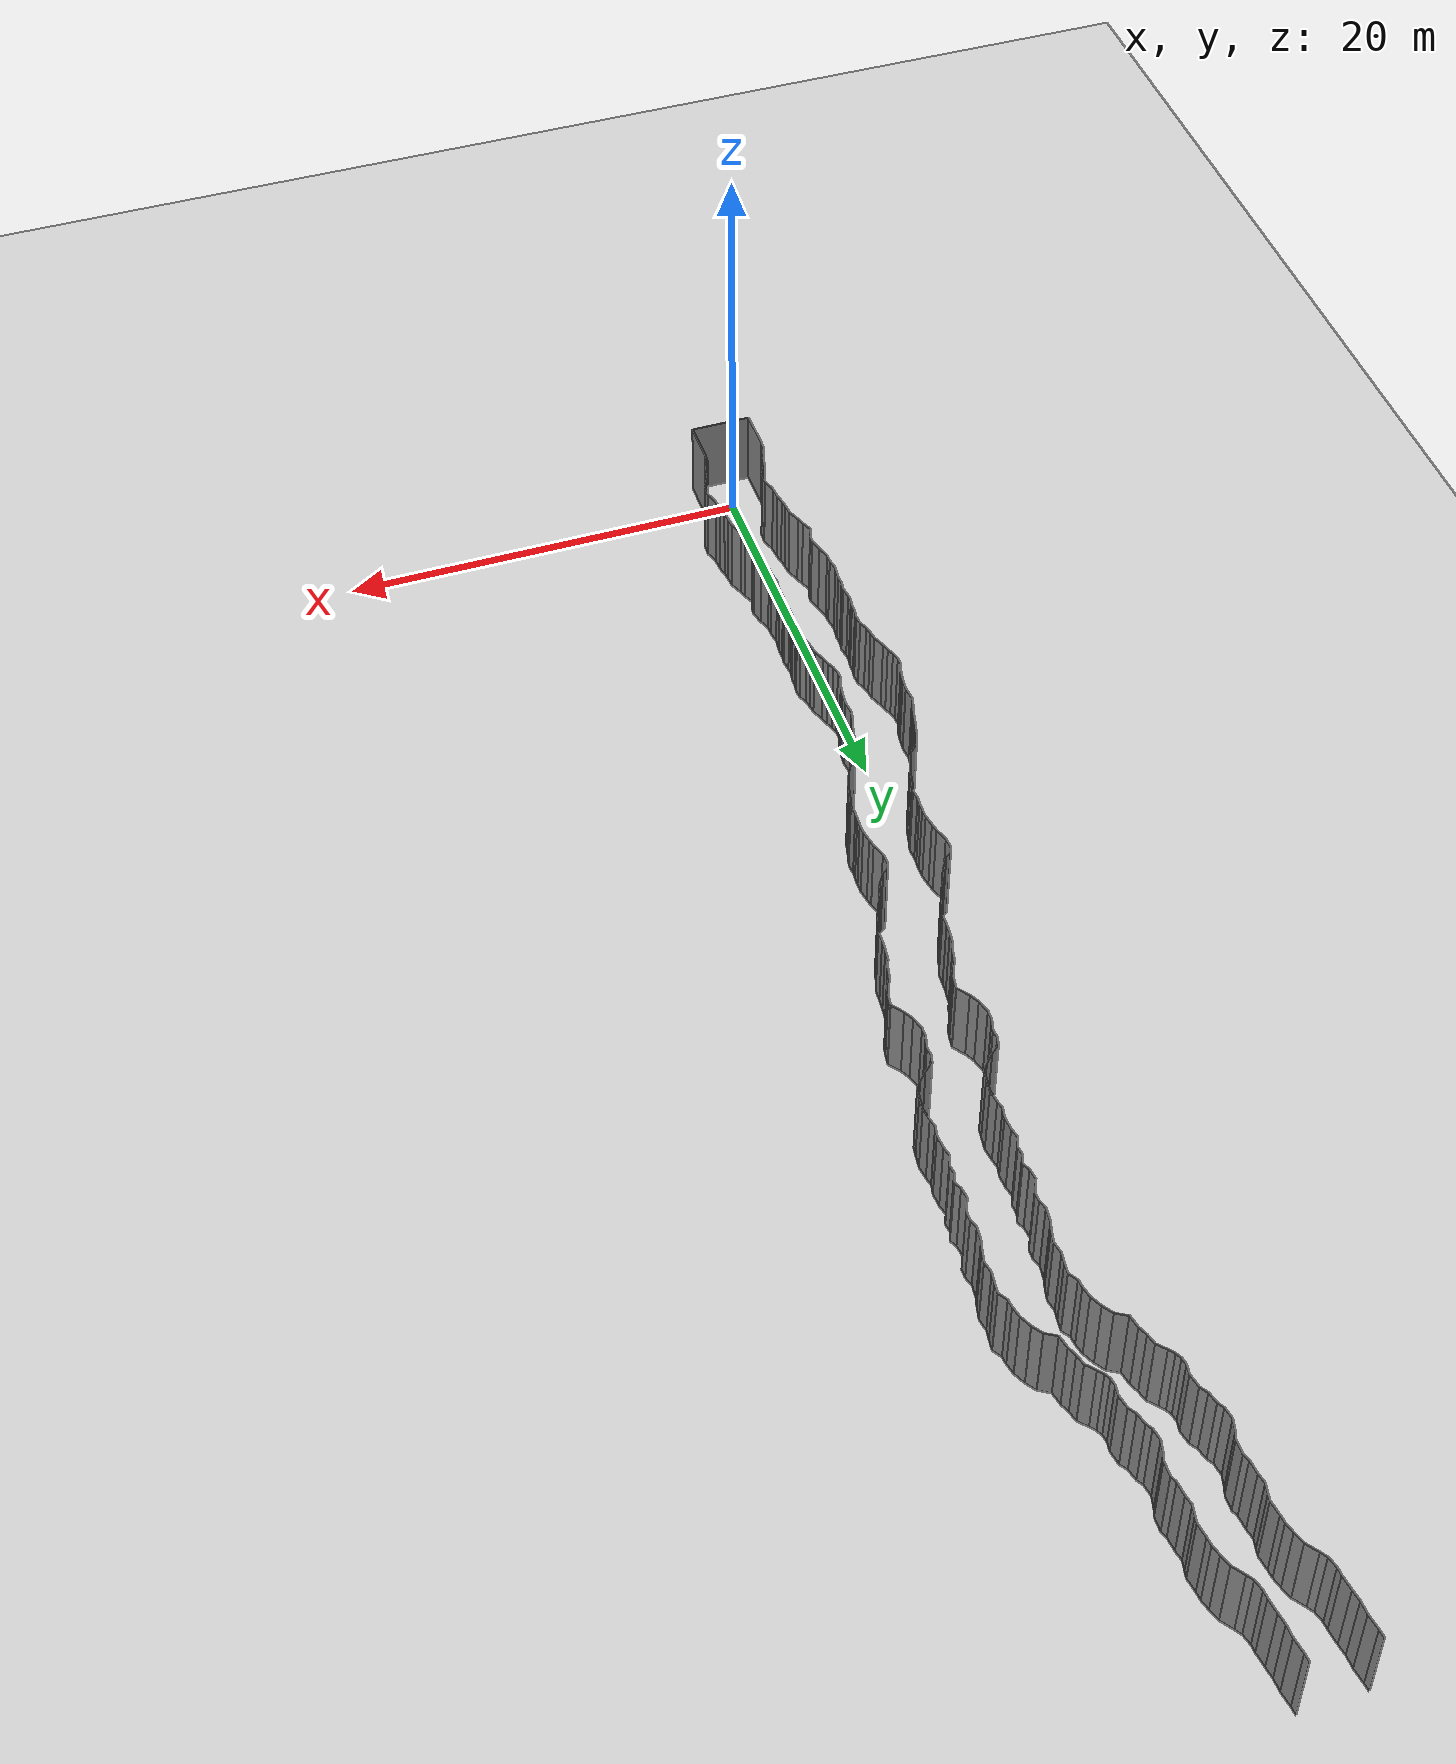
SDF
<sdf version="1.6">
 <world name="default">
  <light name="sun" type="directional">
   <pose>0 0 10 0 -0 0</pose>
   <diffuse>0.8 0.8 0.8 1</diffuse>
   <specular>0.2 0.2 0.2 1</specular>
   <attenuation>
    <range>1000</range>
    <constant>0.9</constant>
    <linear>0.01</linear>
    <quadratic>0.001</quadratic>
   </attenuation>
   <direction>-0.5 0.1 -0.9</direction>
  </light>
  <model name="ground_plane">
   <static>1</static>
   <link name="link">
    <collision name="collision">
     <geometry><plane><normal>0 0 1</normal><size>200 200</size></plane></geometry>
     <surface><friction><ode><mu>100</mu><mu2>50</mu2></ode></friction></surface>
    </collision>
    <visual name="visual">
     <cast_shadows>0</cast_shadows>
     <geometry><plane><normal>0 0 1</normal><size>200 200</size></plane></geometry>
     <material>
      <script><uri>file://media/materials/scripts/gazebo.material</uri><name>Gazebo/Grey</name></script>
     </material>
    </visual>
   </link>
   <pose>0 100 0 0 -0 0</pose>
  </model>
  <gravity>0 0 -9.8</gravity>
  <magnetic_field>6e-06 2.3e-05 -4.2e-05</magnetic_field>
  <atmosphere type="adiabatic"/>
  <physics default="0" name="default_physics" type="ode">
   <max_step_size>0.001</max_step_size>
   <real_time_factor>1</real_time_factor>
   <real_time_update_rate>1000</real_time_update_rate>
  </physics>
  <scene><ambient>0.4 0.4 0.4 1</ambient><background>0.7 0.7 0.7 1</background><shadows>1</shadows></scene>
  <spherical_coordinates>
   <surface_model>EARTH_WGS84</surface_model>
   <latitude_deg>0</latitude_deg>
   <longitude_deg>0</longitude_deg>
   <elevation>0</elevation>
   <heading_deg>0</heading_deg>
  </spherical_coordinates>
  <model name="wall_back">
   <static>1</static>
   <pose>0.0 -2 2 0.0 0 0.0</pose>
   <link name="link">
    <collision name="collision"><geometry><box><size>3 0.02 4</size></box></geometry></collision>
    <visual name="visual">
     <material>
      <script><name>Gazebo/Grey</name><uri>file://media/materials/scripts/gazebo.material</uri></script>
     </material>
     <geometry><box><size>3 0.02 4</size></box></geometry>
    </visual>
   </link>
  </model>
  <model name="wall_left">
   <static>1</static>
   <pose>1.5 -1 2 0 0 0.00</pose>
   <link name="link">
    <collision name="collision"><geometry><box><size>0.02 2 4</size></box></geometry></collision>
    <visual name="visual">
     <material>
      <script><name>Gazebo/Grey</name><uri>file://media/materials/scripts/gazebo.material</uri></script>
     </material>
     <geometry><box><size>0.02 2 4</size></box></geometry>
    </visual>
   </link>
  </model>
  <model name="wall_right">
   <static>1</static>
   <pose>-1.5 -1 2 0 0 0.00</pose>
   <link name="link">
    <collision name="collision"><geometry><box><size>0.02 2 4</size></box></geometry></collision>
    <visual name="visual">
     <material>
      <script><name>Gazebo/Grey</name><uri>file://media/materials/scripts/gazebo.material</uri></script>
     </material>
     <geometry><box><size>0.02 2 4</size></box></geometry>
    </visual>
   </link>
  </model>
  <model name="wall_0">
   <static>1</static>
   <pose>-1.4806505816911582 0.2638760078779775 2 0 0 -0.07319668671021085</pose>
   <link name="link">
    <collision name="collision"><geometry><box><size>0.02 0.52916896176 4</size></box></geometry></collision>
    <visual name="visual">
     <material>
      <script><name>Gazebo/Grey</name><uri>file://media/materials/scripts/gazebo.material</uri></script>
     </material>
     <geometry><box><size>0.02 0.52916896176 4</size></box></geometry>
    </visual>
   </link>
  </model>
  <model name="wall_1">
   <static>1</static>
   <pose>1.5193494183088418 0.2638760078779775 2 0 0 -0.07319668671021085</pose>
   <link name="link">
    <collision name="collision"><geometry><box><size>0.02 0.52916896176 4</size></box></geometry></collision>
    <visual name="visual">
     <material>
      <script><name>Gazebo/Grey</name><uri>file://media/materials/scripts/gazebo.material</uri></script>
     </material>
     <geometry><box><size>0.02 0.52916896176 4</size></box></geometry>
    </visual>
   </link>
  </model>
  <model name="wall_2">
   <static>1</static>
   <pose>-1.3347677560443025 0.8451626978386627 2 0 0 -0.3793356239943414</pose>
   <link name="link">
    <collision name="collision"><geometry><box><size>0.02 0.683403963327 4</size></box></geometry></collision>
    <visual name="visual">
     <material>
      <script><name>Gazebo/Grey</name><uri>file://media/materials/scripts/gazebo.material</uri></script>
     </material>
     <geometry><box><size>0.02 0.683403963327 4</size></box></geometry>
    </visual>
   </link>
  </model>
  <model name="wall_3">
   <static>1</static>
   <pose>1.6652322439556975 0.8451626978386627 2 0 0 -0.3793356239943414</pose>
   <link name="link">
    <collision name="collision"><geometry><box><size>0.02 0.683403963327 4</size></box></geometry></collision>
    <visual name="visual">
     <material>
      <script><name>Gazebo/Grey</name><uri>file://media/materials/scripts/gazebo.material</uri></script>
     </material>
     <geometry><box><size>0.02 0.683403963327 4</size></box></geometry>
    </visual>
   </link>
  </model>
  <model name="wall_4">
   <static>1</static>
   <pose>-1.1574966765008337 1.427560702445053 2 0 0 -0.18918234575141468</pose>
   <link name="link">
    <collision name="collision"><geometry><box><size>0.02 0.539602047732 4</size></box></geometry></collision>
    <visual name="visual">
     <material>
      <script><name>Gazebo/Grey</name><uri>file://media/materials/scripts/gazebo.material</uri></script>
     </material>
     <geometry><box><size>0.02 0.539602047732 4</size></box></geometry>
    </visual>
   </link>
  </model>
  <model name="wall_5">
   <static>1</static>
   <pose>1.8425033234991663 1.427560702445053 2 0 0 -0.18918234575141468</pose>
   <link name="link">
    <collision name="collision"><geometry><box><size>0.02 0.539602047732 4</size></box></geometry></collision>
    <visual name="visual">
     <material>
      <script><name>Gazebo/Grey</name><uri>file://media/materials/scripts/gazebo.material</uri></script>
     </material>
     <geometry><box><size>0.02 0.539602047732 4</size></box></geometry>
    </visual>
   </link>
  </model>
  <model name="wall_6">
   <static>1</static>
   <pose>-1.018175248905752 1.8668594782574415 2 0 0 -0.47018002745150633</pose>
   <link name="link">
    <collision name="collision"><geometry><box><size>0.02 0.391057870227 4</size></box></geometry></collision>
    <visual name="visual">
     <material>
      <script><name>Gazebo/Grey</name><uri>file://media/materials/scripts/gazebo.material</uri></script>
     </material>
     <geometry><box><size>0.02 0.391057870227 4</size></box></geometry>
    </visual>
   </link>
  </model>
  <model name="wall_7">
   <static>1</static>
   <pose>1.981824751094248 1.8668594782574415 2 0 0 -0.47018002745150633</pose>
   <link name="link">
    <collision name="collision"><geometry><box><size>0.02 0.391057870227 4</size></box></geometry></collision>
    <visual name="visual">
     <material>
      <script><name>Gazebo/Grey</name><uri>file://media/materials/scripts/gazebo.material</uri></script>
     </material>
     <geometry><box><size>0.02 0.391057870227 4</size></box></geometry>
    </visual>
   </link>
  </model>
  <model name="wall_8">
   <static>1</static>
   <pose>-0.8187151531529959 2.243682264581633 2 0 0 -0.5009270629662687</pose>
   <link name="link">
    <collision name="collision"><geometry><box><size>0.02 0.461754925735 4</size></box></geometry></collision>
    <visual name="visual">
     <material>
      <script><name>Gazebo/Grey</name><uri>file://media/materials/scripts/gazebo.material</uri></script>
     </material>
     <geometry><box><size>0.02 0.461754925735 4</size></box></geometry>
    </visual>
   </link>
  </model>
  <model name="wall_9">
   <static>1</static>
   <pose>2.181284846847004 2.243682264581633 2 0 0 -0.5009270629662687</pose>
   <link name="link">
    <collision name="collision"><geometry><box><size>0.02 0.461754925735 4</size></box></geometry></collision>
    <visual name="visual">
     <material>
      <script><name>Gazebo/Grey</name><uri>file://media/materials/scripts/gazebo.material</uri></script>
     </material>
     <geometry><box><size>0.02 0.461754925735 4</size></box></geometry>
    </visual>
   </link>
  </model>
  <model name="wall_10">
   <static>1</static>
   <pose>-0.699499163627389 2.701210871615846 2 0 0 -0.03269064099146519</pose>
   <link name="link">
    <collision name="collision"><geometry><box><size>0.02 0.510307200756 4</size></box></geometry></collision>
    <visual name="visual">
     <material>
      <script><name>Gazebo/Grey</name><uri>file://media/materials/scripts/gazebo.material</uri></script>
     </material>
     <geometry><box><size>0.02 0.510307200756 4</size></box></geometry>
    </visual>
   </link>
  </model>
  <model name="wall_11">
   <static>1</static>
   <pose>2.300500836372611 2.701210871615846 2 0 0 -0.03269064099146519</pose>
   <link name="link">
    <collision name="collision"><geometry><box><size>0.02 0.510307200756 4</size></box></geometry></collision>
    <visual name="visual">
     <material>
      <script><name>Gazebo/Grey</name><uri>file://media/materials/scripts/gazebo.material</uri></script>
     </material>
     <geometry><box><size>0.02 0.510307200756 4</size></box></geometry>
    </visual>
   </link>
  </model>
  <model name="wall_12">
   <static>1</static>
   <pose>-0.7886705382312041 3.288972228835625 2 0 0 0.28506953916078176</pose>
   <link name="link">
    <collision name="collision"><geometry><box><size>0.02 0.693475377139 4</size></box></geometry></collision>
    <visual name="visual">
     <material>
      <script><name>Gazebo/Grey</name><uri>file://media/materials/scripts/gazebo.material</uri></script>
     </material>
     <geometry><box><size>0.02 0.693475377139 4</size></box></geometry>
    </visual>
   </link>
  </model>
  <model name="wall_13">
   <static>1</static>
   <pose>2.2113294617687957 3.288972228835625 2 0 0 0.28506953916078176</pose>
   <link name="link">
    <collision name="collision"><geometry><box><size>0.02 0.693475377139 4</size></box></geometry></collision>
    <visual name="visual">
     <material>
      <script><name>Gazebo/Grey</name><uri>file://media/materials/scripts/gazebo.material</uri></script>
     </material>
     <geometry><box><size>0.02 0.693475377139 4</size></box></geometry>
    </visual>
   </link>
  </model>
  <model name="wall_14">
   <static>1</static>
   <pose>-0.9032436255926277 3.926684897969823 2 0 0 0.05588869139170713</pose>
   <link name="link">
    <collision name="collision"><geometry><box><size>0.02 0.610890996522 4</size></box></geometry></collision>
    <visual name="visual">
     <material>
      <script><name>Gazebo/Grey</name><uri>file://media/materials/scripts/gazebo.material</uri></script>
     </material>
     <geometry><box><size>0.02 0.610890996522 4</size></box></geometry>
    </visual>
   </link>
  </model>
  <model name="wall_15">
   <static>1</static>
   <pose>2.0967563744073723 3.926684897969823 2 0 0 0.05588869139170713</pose>
   <link name="link">
    <collision name="collision"><geometry><box><size>0.02 0.610890996522 4</size></box></geometry></collision>
    <visual name="visual">
     <material>
      <script><name>Gazebo/Grey</name><uri>file://media/materials/scripts/gazebo.material</uri></script>
     </material>
     <geometry><box><size>0.02 0.610890996522 4</size></box></geometry>
    </visual>
   </link>
  </model>
  <model name="wall_16">
   <static>1</static>
   <pose>-0.9632969751219683 4.437540530153037 2 0 0 0.20585223921532592</pose>
   <link name="link">
    <collision name="collision"><geometry><box><size>0.02 0.420655329162 4</size></box></geometry></collision>
    <visual name="visual">
     <material>
      <script><name>Gazebo/Grey</name><uri>file://media/materials/scripts/gazebo.material</uri></script>
     </material>
     <geometry><box><size>0.02 0.420655329162 4</size></box></geometry>
    </visual>
   </link>
  </model>
  <model name="wall_17">
   <static>1</static>
   <pose>2.036703024878032 4.437540530153037 2 0 0 0.20585223921532592</pose>
   <link name="link">
    <collision name="collision"><geometry><box><size>0.02 0.420655329162 4</size></box></geometry></collision>
    <visual name="visual">
     <material>
      <script><name>Gazebo/Grey</name><uri>file://media/materials/scripts/gazebo.material</uri></script>
     </material>
     <geometry><box><size>0.02 0.420655329162 4</size></box></geometry>
    </visual>
   </link>
  </model>
  <model name="wall_18">
   <static>1</static>
   <pose>-1.0332514346551713 4.836432062273257 2 0 0 0.13880396763324238</pose>
   <link name="link">
    <collision name="collision"><geometry><box><size>0.02 0.389757587681 4</size></box></geometry></collision>
    <visual name="visual">
     <material>
      <script><name>Gazebo/Grey</name><uri>file://media/materials/scripts/gazebo.material</uri></script>
     </material>
     <geometry><box><size>0.02 0.389757587681 4</size></box></geometry>
    </visual>
   </link>
  </model>
  <model name="wall_19">
   <static>1</static>
   <pose>1.9667485653448287 4.836432062273257 2 0 0 0.13880396763324238</pose>
   <link name="link">
    <collision name="collision"><geometry><box><size>0.02 0.389757587681 4</size></box></geometry></collision>
    <visual name="visual">
     <material>
      <script><name>Gazebo/Grey</name><uri>file://media/materials/scripts/gazebo.material</uri></script>
     </material>
     <geometry><box><size>0.02 0.389757587681 4</size></box></geometry>
    </visual>
   </link>
  </model>
  <model name="wall_20">
   <static>1</static>
   <pose>-1.0778982370499175 5.289179252299811 2 0 0 0.0679764345224434</pose>
   <link name="link">
    <collision name="collision"><geometry><box><size>0.02 0.520687941478 4</size></box></geometry></collision>
    <visual name="visual">
     <material>
      <script><name>Gazebo/Grey</name><uri>file://media/materials/scripts/gazebo.material</uri></script>
     </material>
     <geometry><box><size>0.02 0.520687941478 4</size></box></geometry>
    </visual>
   </link>
  </model>
  <model name="wall_21">
   <static>1</static>
   <pose>1.9221017629500825 5.289179252299811 2 0 0 0.0679764345224434</pose>
   <link name="link">
    <collision name="collision"><geometry><box><size>0.02 0.520687941478 4</size></box></geometry></collision>
    <visual name="visual">
     <material>
      <script><name>Gazebo/Grey</name><uri>file://media/materials/scripts/gazebo.material</uri></script>
     </material>
     <geometry><box><size>0.02 0.520687941478 4</size></box></geometry>
    </visual>
   </link>
  </model>
  <model name="wall_22">
   <static>1</static>
   <pose>-1.2184899678075378 5.859696038116188 2 0 0 0.37661257804343046</pose>
   <link name="link">
    <collision name="collision"><geometry><box><size>0.02 0.668391895065 4</size></box></geometry></collision>
    <visual name="visual">
     <material>
      <script><name>Gazebo/Grey</name><uri>file://media/materials/scripts/gazebo.material</uri></script>
     </material>
     <geometry><box><size>0.02 0.668391895065 4</size></box></geometry>
    </visual>
   </link>
  </model>
  <model name="wall_23">
   <static>1</static>
   <pose>1.7815100321924622 5.859696038116188 2 0 0 0.37661257804343046</pose>
   <link name="link">
    <collision name="collision"><geometry><box><size>0.02 0.668391895065 4</size></box></geometry></collision>
    <visual name="visual">
     <material>
      <script><name>Gazebo/Grey</name><uri>file://media/materials/scripts/gazebo.material</uri></script>
     </material>
     <geometry><box><size>0.02 0.668391895065 4</size></box></geometry>
    </visual>
   </link>
  </model>
  <model name="wall_24">
   <static>1</static>
   <pose>-1.3963707065241764 6.357607284663069 2 0 0 0.28571841662320563</pose>
   <link name="link">
    <collision name="collision"><geometry><box><size>0.02 0.390088755445 4</size></box></geometry></collision>
    <visual name="visual">
     <material>
      <script><name>Gazebo/Grey</name><uri>file://media/materials/scripts/gazebo.material</uri></script>
     </material>
     <geometry><box><size>0.02 0.390088755445 4</size></box></geometry>
    </visual>
   </link>
  </model>
  <model name="wall_25">
   <static>1</static>
   <pose>1.6036292934758236 6.357607284663069 2 0 0 0.28571841662320563</pose>
   <link name="link">
    <collision name="collision"><geometry><box><size>0.02 0.390088755445 4</size></box></geometry></collision>
    <visual name="visual">
     <material>
      <script><name>Gazebo/Grey</name><uri>file://media/materials/scripts/gazebo.material</uri></script>
     </material>
     <geometry><box><size>0.02 0.390088755445 4</size></box></geometry>
    </visual>
   </link>
  </model>
  <model name="wall_26">
   <static>1</static>
   <pose>-1.5641696388041426 6.797914586991042 2 0 0 0.41923395385083295</pose>
   <link name="link">
    <collision name="collision"><geometry><box><size>0.02 0.554346070406 4</size></box></geometry></collision>
    <visual name="visual">
     <material>
      <script><name>Gazebo/Grey</name><uri>file://media/materials/scripts/gazebo.material</uri></script>
     </material>
     <geometry><box><size>0.02 0.554346070406 4</size></box></geometry>
    </visual>
   </link>
  </model>
  <model name="wall_27">
   <static>1</static>
   <pose>1.4358303611958574 6.797914586991042 2 0 0 0.41923395385083295</pose>
   <link name="link">
    <collision name="collision"><geometry><box><size>0.02 0.554346070406 4</size></box></geometry></collision>
    <visual name="visual">
     <material>
      <script><name>Gazebo/Grey</name><uri>file://media/materials/scripts/gazebo.material</uri></script>
     </material>
     <geometry><box><size>0.02 0.554346070406 4</size></box></geometry>
    </visual>
   </link>
  </model>
  <model name="wall_28">
   <static>1</static>
   <pose>-1.5715556928346086 7.294797096098278 2 0 0 -0.4083257589642621</pose>
   <link name="link">
    <collision name="collision"><geometry><box><size>0.02 0.531087053653 4</size></box></geometry></collision>
    <visual name="visual">
     <material>
      <script><name>Gazebo/Grey</name><uri>file://media/materials/scripts/gazebo.material</uri></script>
     </material>
     <geometry><box><size>0.02 0.531087053653 4</size></box></geometry>
    </visual>
   </link>
  </model>
  <model name="wall_29">
   <static>1</static>
   <pose>1.4284443071653914 7.294797096098278 2 0 0 -0.4083257589642621</pose>
   <link name="link">
    <collision name="collision"><geometry><box><size>0.02 0.531087053653 4</size></box></geometry></collision>
    <visual name="visual">
     <material>
      <script><name>Gazebo/Grey</name><uri>file://media/materials/scripts/gazebo.material</uri></script>
     </material>
     <geometry><box><size>0.02 0.531087053653 4</size></box></geometry>
    </visual>
   </link>
  </model>
  <model name="wall_30">
   <static>1</static>
   <pose>-1.4531127868125584 7.728849146482762 2 0 0 -0.06820697990331713</pose>
   <link name="link">
    <collision name="collision"><geometry><box><size>0.02 0.38156657386 4</size></box></geometry></collision>
    <visual name="visual">
     <material>
      <script><name>Gazebo/Grey</name><uri>file://media/materials/scripts/gazebo.material</uri></script>
     </material>
     <geometry><box><size>0.02 0.38156657386 4</size></box></geometry>
    </visual>
   </link>
  </model>
  <model name="wall_31">
   <static>1</static>
   <pose>1.5468872131874416 7.728849146482762 2 0 0 -0.06820697990331713</pose>
   <link name="link">
    <collision name="collision"><geometry><box><size>0.02 0.38156657386 4</size></box></geometry></collision>
    <visual name="visual">
     <material>
      <script><name>Gazebo/Grey</name><uri>file://media/materials/scripts/gazebo.material</uri></script>
     </material>
     <geometry><box><size>0.02 0.38156657386 4</size></box></geometry>
    </visual>
   </link>
  </model>
  <model name="wall_32">
   <static>1</static>
   <pose>-1.5222561957525884 8.230989704984943 2 0 0 0.25760327481442136</pose>
   <link name="link">
    <collision name="collision"><geometry><box><size>0.02 0.644880658828 4</size></box></geometry></collision>
    <visual name="visual">
     <material>
      <script><name>Gazebo/Grey</name><uri>file://media/materials/scripts/gazebo.material</uri></script>
     </material>
     <geometry><box><size>0.02 0.644880658828 4</size></box></geometry>
    </visual>
   </link>
  </model>
  <model name="wall_33">
   <static>1</static>
   <pose>1.4777438042474116 8.230989704984943 2 0 0 0.25760327481442136</pose>
   <link name="link">
    <collision name="collision"><geometry><box><size>0.02 0.644880658828 4</size></box></geometry></collision>
    <visual name="visual">
     <material>
      <script><name>Gazebo/Grey</name><uri>file://media/materials/scripts/gazebo.material</uri></script>
     </material>
     <geometry><box><size>0.02 0.644880658828 4</size></box></geometry>
    </visual>
   </link>
  </model>
  <model name="wall_34">
   <static>1</static>
   <pose>-1.6977240495216837 8.836065523477549 2 0 0 0.3080745388373704</pose>
   <link name="link">
    <collision name="collision"><geometry><box><size>0.02 0.615529509744 4</size></box></geometry></collision>
    <visual name="visual">
     <material>
      <script><name>Gazebo/Grey</name><uri>file://media/materials/scripts/gazebo.material</uri></script>
     </material>
     <geometry><box><size>0.02 0.615529509744 4</size></box></geometry>
    </visual>
   </link>
  </model>
  <model name="wall_35">
   <static>1</static>
   <pose>1.3022759504783163 8.836065523477549 2 0 0 0.3080745388373704</pose>
   <link name="link">
    <collision name="collision"><geometry><box><size>0.02 0.615529509744 4</size></box></geometry></collision>
    <visual name="visual">
     <material>
      <script><name>Gazebo/Grey</name><uri>file://media/materials/scripts/gazebo.material</uri></script>
     </material>
     <geometry><box><size>0.02 0.615529509744 4</size></box></geometry>
    </visual>
   </link>
  </model>
  <model name="wall_36">
   <static>1</static>
   <pose>-1.7900697899834113 9.332865241432385 2 0 0 -0.004795643857899882</pose>
   <link name="link">
    <collision name="collision"><geometry><box><size>0.02 0.407054239281 4</size></box></geometry></collision>
    <visual name="visual">
     <material>
      <script><name>Gazebo/Grey</name><uri>file://media/materials/scripts/gazebo.material</uri></script>
     </material>
     <geometry><box><size>0.02 0.407054239281 4</size></box></geometry>
    </visual>
   </link>
  </model>
  <model name="wall_37">
   <static>1</static>
   <pose>1.2099302100165887 9.332865241432385 2 0 0 -0.004795643857899882</pose>
   <link name="link">
    <collision name="collision"><geometry><box><size>0.02 0.407054239281 4</size></box></geometry></collision>
    <visual name="visual">
     <material>
      <script><name>Gazebo/Grey</name><uri>file://media/materials/scripts/gazebo.material</uri></script>
     </material>
     <geometry><box><size>0.02 0.407054239281 4</size></box></geometry>
    </visual>
   </link>
  </model>
  <model name="wall_38">
   <static>1</static>
   <pose>-1.8290855316536374 9.826789955649428 2 0 0 0.1368519854148838</pose>
   <link name="link">
    <collision name="collision"><geometry><box><size>0.02 0.5862813823 4</size></box></geometry></collision>
    <visual name="visual">
     <material>
      <script><name>Gazebo/Grey</name><uri>file://media/materials/scripts/gazebo.material</uri></script>
     </material>
     <geometry><box><size>0.02 0.5862813823 4</size></box></geometry>
    </visual>
   </link>
  </model>
  <model name="wall_39">
   <static>1</static>
   <pose>1.1709144683463626 9.826789955649428 2 0 0 0.1368519854148838</pose>
   <link name="link">
    <collision name="collision"><geometry><box><size>0.02 0.5862813823 4</size></box></geometry></collision>
    <visual name="visual">
     <material>
      <script><name>Gazebo/Grey</name><uri>file://media/materials/scripts/gazebo.material</uri></script>
     </material>
     <geometry><box><size>0.02 0.5862813823 4</size></box></geometry>
    </visual>
   </link>
  </model>
  <model name="wall_40">
   <static>1</static>
   <pose>-1.8211837255270784 10.460243788075154 2 0 0 -0.13871294060656478</pose>
   <link name="link">
    <collision name="collision"><geometry><box><size>0.02 0.692761928253 4</size></box></geometry></collision>
    <visual name="visual">
     <material>
      <script><name>Gazebo/Grey</name><uri>file://media/materials/scripts/gazebo.material</uri></script>
     </material>
     <geometry><box><size>0.02 0.692761928253 4</size></box></geometry>
    </visual>
   </link>
  </model>
  <model name="wall_41">
   <static>1</static>
   <pose>1.1788162744729216 10.460243788075154 2 0 0 -0.13871294060656478</pose>
   <link name="link">
    <collision name="collision"><geometry><box><size>0.02 0.692761928253 4</size></box></geometry></collision>
    <visual name="visual">
     <material>
      <script><name>Gazebo/Grey</name><uri>file://media/materials/scripts/gazebo.material</uri></script>
     </material>
     <geometry><box><size>0.02 0.692761928253 4</size></box></geometry>
    </visual>
   </link>
  </model>
  <model name="wall_42">
   <static>1</static>
   <pose>-1.7820610402955435 11.017080949439686 2 0 0 0.04100408089633034</pose>
   <link name="link">
    <collision name="collision"><geometry><box><size>0.02 0.42792622097 4</size></box></geometry></collision>
    <visual name="visual">
     <material>
      <script><name>Gazebo/Grey</name><uri>file://media/materials/scripts/gazebo.material</uri></script>
     </material>
     <geometry><box><size>0.02 0.42792622097 4</size></box></geometry>
    </visual>
   </link>
  </model>
  <model name="wall_43">
   <static>1</static>
   <pose>1.2179389597044565 11.017080949439686 2 0 0 0.04100408089633034</pose>
   <link name="link">
    <collision name="collision"><geometry><box><size>0.02 0.42792622097 4</size></box></geometry></collision>
    <visual name="visual">
     <material>
      <script><name>Gazebo/Grey</name><uri>file://media/materials/scripts/gazebo.material</uri></script>
     </material>
     <geometry><box><size>0.02 0.42792622097 4</size></box></geometry>
    </visual>
   </link>
  </model>
  <model name="wall_44">
   <static>1</static>
   <pose>-1.7545526363760067 11.448993846082535 2 0 0 -0.16481129784456724</pose>
   <link name="link">
    <collision name="collision"><geometry><box><size>0.02 0.44225207632 4</size></box></geometry></collision>
    <visual name="visual">
     <material>
      <script><name>Gazebo/Grey</name><uri>file://media/materials/scripts/gazebo.material</uri></script>
     </material>
     <geometry><box><size>0.02 0.44225207632 4</size></box></geometry>
    </visual>
   </link>
  </model>
  <model name="wall_45">
   <static>1</static>
   <pose>1.2454473636239933 11.448993846082535 2 0 0 -0.16481129784456724</pose>
   <link name="link">
    <collision name="collision"><geometry><box><size>0.02 0.44225207632 4</size></box></geometry></collision>
    <visual name="visual">
     <material>
      <script><name>Gazebo/Grey</name><uri>file://media/materials/scripts/gazebo.material</uri></script>
     </material>
     <geometry><box><size>0.02 0.44225207632 4</size></box></geometry>
    </visual>
   </link>
  </model>
  <model name="wall_46">
   <static>1</static>
   <pose>-1.7539616690065436 11.916115314415272 2 0 0 0.14236175861577385</pose>
   <link name="link">
    <collision name="collision"><geometry><box><size>0.02 0.503072924029 4</size></box></geometry></collision>
    <visual name="visual">
     <material>
      <script><name>Gazebo/Grey</name><uri>file://media/materials/scripts/gazebo.material</uri></script>
     </material>
     <geometry><box><size>0.02 0.503072924029 4</size></box></geometry>
    </visual>
   </link>
  </model>
  <model name="wall_47">
   <static>1</static>
   <pose>1.2460383309934564 11.916115314415272 2 0 0 0.14236175861577385</pose>
   <link name="link">
    <collision name="collision"><geometry><box><size>0.02 0.503072924029 4</size></box></geometry></collision>
    <visual name="visual">
     <material>
      <script><name>Gazebo/Grey</name><uri>file://media/materials/scripts/gazebo.material</uri></script>
     </material>
     <geometry><box><size>0.02 0.503072924029 4</size></box></geometry>
    </visual>
   </link>
  </model>
  <model name="wall_48">
   <static>1</static>
   <pose>-1.7937694805933937 12.343922469897969 2 0 0 0.0230335079206646</pose>
   <link name="link">
    <collision name="collision"><geometry><box><size>0.02 0.357725529907 4</size></box></geometry></collision>
    <visual name="visual">
     <material>
      <script><name>Gazebo/Grey</name><uri>file://media/materials/scripts/gazebo.material</uri></script>
     </material>
     <geometry><box><size>0.02 0.357725529907 4</size></box></geometry>
    </visual>
   </link>
  </model>
  <model name="wall_49">
   <static>1</static>
   <pose>1.2062305194066063 12.343922469897969 2 0 0 0.0230335079206646</pose>
   <link name="link">
    <collision name="collision"><geometry><box><size>0.02 0.357725529907 4</size></box></geometry></collision>
    <visual name="visual">
     <material>
      <script><name>Gazebo/Grey</name><uri>file://media/materials/scripts/gazebo.material</uri></script>
     </material>
     <geometry><box><size>0.02 0.357725529907 4</size></box></geometry>
    </visual>
   </link>
  </model>
  <model name="wall_50">
   <static>1</static>
   <pose>-1.7545245136025849 12.723348766916374 2 0 0 -0.2128864093295695</pose>
   <link name="link">
    <collision name="collision"><geometry><box><size>0.02 0.410488678348 4</size></box></geometry></collision>
    <visual name="visual">
     <material>
      <script><name>Gazebo/Grey</name><uri>file://media/materials/scripts/gazebo.material</uri></script>
     </material>
     <geometry><box><size>0.02 0.410488678348 4</size></box></geometry>
    </visual>
   </link>
  </model>
  <model name="wall_51">
   <static>1</static>
   <pose>1.2454754863974151 12.723348766916374 2 0 0 -0.2128864093295695</pose>
   <link name="link">
    <collision name="collision"><geometry><box><size>0.02 0.410488678348 4</size></box></geometry></collision>
    <visual name="visual">
     <material>
      <script><name>Gazebo/Grey</name><uri>file://media/materials/scripts/gazebo.material</uri></script>
     </material>
     <geometry><box><size>0.02 0.410488678348 4</size></box></geometry>
    </visual>
   </link>
  </model>
  <model name="wall_52">
   <static>1</static>
   <pose>-1.707073501311995 13.151512796722969 2 0 0 -0.01795683852493344</pose>
   <link name="link">
    <collision name="collision"><geometry><box><size>0.02 0.45517948928 4</size></box></geometry></collision>
    <visual name="visual">
     <material>
      <script><name>Gazebo/Grey</name><uri>file://media/materials/scripts/gazebo.material</uri></script>
     </material>
     <geometry><box><size>0.02 0.45517948928 4</size></box></geometry>
    </visual>
   </link>
  </model>
  <model name="wall_53">
   <static>1</static>
   <pose>1.292926498688005 13.151512796722969 2 0 0 -0.01795683852493344</pose>
   <link name="link">
    <collision name="collision"><geometry><box><size>0.02 0.45517948928 4</size></box></geometry></collision>
    <visual name="visual">
     <material>
      <script><name>Gazebo/Grey</name><uri>file://media/materials/scripts/gazebo.material</uri></script>
     </material>
     <geometry><box><size>0.02 0.45517948928 4</size></box></geometry>
    </visual>
   </link>
  </model>
  <model name="wall_54">
   <static>1</static>
   <pose>-1.6729093456068864 13.547182709813656 2 0 0 -0.17703576717036326</pose>
   <link name="link">
    <collision name="collision"><geometry><box><size>0.02 0.341572479874 4</size></box></geometry></collision>
    <visual name="visual">
     <material>
      <script><name>Gazebo/Grey</name><uri>file://media/materials/scripts/gazebo.material</uri></script>
     </material>
     <geometry><box><size>0.02 0.341572479874 4</size></box></geometry>
    </visual>
   </link>
  </model>
  <model name="wall_55">
   <static>1</static>
   <pose>1.3270906543931136 13.547182709813656 2 0 0 -0.17703576717036326</pose>
   <link name="link">
    <collision name="collision"><geometry><box><size>0.02 0.341572479874 4</size></box></geometry></collision>
    <visual name="visual">
     <material>
      <script><name>Gazebo/Grey</name><uri>file://media/materials/scripts/gazebo.material</uri></script>
     </material>
     <geometry><box><size>0.02 0.341572479874 4</size></box></geometry>
    </visual>
   </link>
  </model>
  <model name="wall_56">
   <static>1</static>
   <pose>-1.6562424079520828 13.950159059017647 2 0 0 0.057038780066605795</pose>
   <link name="link">
    <collision name="collision"><geometry><box><size>0.02 0.470484111915 4</size></box></geometry></collision>
    <visual name="visual">
     <material>
      <script><name>Gazebo/Grey</name><uri>file://media/materials/scripts/gazebo.material</uri></script>
     </material>
     <geometry><box><size>0.02 0.470484111915 4</size></box></geometry>
    </visual>
   </link>
  </model>
  <model name="wall_57">
   <static>1</static>
   <pose>1.3437575920479172 13.950159059017647 2 0 0 0.057038780066605795</pose>
   <link name="link">
    <collision name="collision"><geometry><box><size>0.02 0.470484111915 4</size></box></geometry></collision>
    <visual name="visual">
     <material>
      <script><name>Gazebo/Grey</name><uri>file://media/materials/scripts/gazebo.material</uri></script>
     </material>
     <geometry><box><size>0.02 0.470484111915 4</size></box></geometry>
    </visual>
   </link>
  </model>
  <model name="wall_58">
   <static>1</static>
   <pose>-1.7538399868780927 14.373468656080588 2 0 0 0.4201339943812786</pose>
   <link name="link">
    <collision name="collision"><geometry><box><size>0.02 0.412799627336 4</size></box></geometry></collision>
    <visual name="visual">
     <material>
      <script><name>Gazebo/Grey</name><uri>file://media/materials/scripts/gazebo.material</uri></script>
     </material>
     <geometry><box><size>0.02 0.412799627336 4</size></box></geometry>
    </visual>
   </link>
  </model>
  <model name="wall_59">
   <static>1</static>
   <pose>1.2461600131219073 14.373468656080588 2 0 0 0.4201339943812786</pose>
   <link name="link">
    <collision name="collision"><geometry><box><size>0.02 0.412799627336 4</size></box></geometry></collision>
    <visual name="visual">
     <material>
      <script><name>Gazebo/Grey</name><uri>file://media/materials/scripts/gazebo.material</uri></script>
     </material>
     <geometry><box><size>0.02 0.412799627336 4</size></box></geometry>
    </visual>
   </link>
  </model>
  <model name="wall_60">
   <static>1</static>
   <pose>-1.8757019489359947 14.763976343141834 2 0 0 0.18434007996588148</pose>
   <link name="link">
    <collision name="collision"><geometry><box><size>0.02 0.411079909143 4</size></box></geometry></collision>
    <visual name="visual">
     <material>
      <script><name>Gazebo/Grey</name><uri>file://media/materials/scripts/gazebo.material</uri></script>
     </material>
     <geometry><box><size>0.02 0.411079909143 4</size></box></geometry>
    </visual>
   </link>
  </model>
  <model name="wall_61">
   <static>1</static>
   <pose>1.1242980510640053 14.763976343141834 2 0 0 0.18434007996588148</pose>
   <link name="link">
    <collision name="collision"><geometry><box><size>0.02 0.411079909143 4</size></box></geometry></collision>
    <visual name="visual">
     <material>
      <script><name>Gazebo/Grey</name><uri>file://media/materials/scripts/gazebo.material</uri></script>
     </material>
     <geometry><box><size>0.02 0.411079909143 4</size></box></geometry>
    </visual>
   </link>
  </model>
  <model name="wall_62">
   <static>1</static>
   <pose>-1.9380992998486257 15.154620653485713 2 0 0 0.130349282143044</pose>
   <link name="link">
    <collision name="collision"><geometry><box><size>0.02 0.380400570652 4</size></box></geometry></collision>
    <visual name="visual">
     <material>
      <script><name>Gazebo/Grey</name><uri>file://media/materials/scripts/gazebo.material</uri></script>
     </material>
     <geometry><box><size>0.02 0.380400570652 4</size></box></geometry>
    </visual>
   </link>
  </model>
  <model name="wall_63">
   <static>1</static>
   <pose>1.0619007001513743 15.154620653485713 2 0 0 0.130349282143044</pose>
   <link name="link">
    <collision name="collision"><geometry><box><size>0.02 0.380400570652 4</size></box></geometry></collision>
    <visual name="visual">
     <material>
      <script><name>Gazebo/Grey</name><uri>file://media/materials/scripts/gazebo.material</uri></script>
     </material>
     <geometry><box><size>0.02 0.380400570652 4</size></box></geometry>
    </visual>
   </link>
  </model>
  <model name="wall_64">
   <static>1</static>
   <pose>-2.075568128735266 15.643693925728725 2 0 0 0.3589575430471233</pose>
   <link name="link">
    <collision name="collision"><geometry><box><size>0.02 0.64188452503 4</size></box></geometry></collision>
    <visual name="visual">
     <material>
      <script><name>Gazebo/Grey</name><uri>file://media/materials/scripts/gazebo.material</uri></script>
     </material>
     <geometry><box><size>0.02 0.64188452503 4</size></box></geometry>
    </visual>
   </link>
  </model>
  <model name="wall_65">
   <static>1</static>
   <pose>0.9244318712647339 15.643693925728725 2 0 0 0.3589575430471233</pose>
   <link name="link">
    <collision name="collision"><geometry><box><size>0.02 0.64188452503 4</size></box></geometry></collision>
    <visual name="visual">
     <material>
      <script><name>Gazebo/Grey</name><uri>file://media/materials/scripts/gazebo.material</uri></script>
     </material>
     <geometry><box><size>0.02 0.64188452503 4</size></box></geometry>
    </visual>
   </link>
  </model>
  <model name="wall_66">
   <static>1</static>
   <pose>-2.2393345266207048 16.126716548847124 2 0 0 0.2725503608674695</pose>
   <link name="link">
    <collision name="collision"><geometry><box><size>0.02 0.379064378185 4</size></box></geometry></collision>
    <visual name="visual">
     <material>
      <script><name>Gazebo/Grey</name><uri>file://media/materials/scripts/gazebo.material</uri></script>
     </material>
     <geometry><box><size>0.02 0.379064378185 4</size></box></geometry>
    </visual>
   </link>
  </model>
  <model name="wall_67">
   <static>1</static>
   <pose>0.7606654733792952 16.126716548847124 2 0 0 0.2725503608674695</pose>
   <link name="link">
    <collision name="collision"><geometry><box><size>0.02 0.379064378185 4</size></box></geometry></collision>
    <visual name="visual">
     <material>
      <script><name>Gazebo/Grey</name><uri>file://media/materials/scripts/gazebo.material</uri></script>
     </material>
     <geometry><box><size>0.02 0.379064378185 4</size></box></geometry>
    </visual>
   </link>
  </model>
  <model name="wall_68">
   <static>1</static>
   <pose>-2.3595510225879344 16.47393807386008 2 0 0 0.39777621847941735</pose>
   <link name="link">
    <collision name="collision"><geometry><box><size>0.02 0.357264412374 4</size></box></geometry></collision>
    <visual name="visual">
     <material>
      <script><name>Gazebo/Grey</name><uri>file://media/materials/scripts/gazebo.material</uri></script>
     </material>
     <geometry><box><size>0.02 0.357264412374 4</size></box></geometry>
    </visual>
   </link>
  </model>
  <model name="wall_69">
   <static>1</static>
   <pose>0.6404489774120656 16.47393807386008 2 0 0 0.39777621847941735</pose>
   <link name="link">
    <collision name="collision"><geometry><box><size>0.02 0.357264412374 4</size></box></geometry></collision>
    <visual name="visual">
     <material>
      <script><name>Gazebo/Grey</name><uri>file://media/materials/scripts/gazebo.material</uri></script>
     </material>
     <geometry><box><size>0.02 0.357264412374 4</size></box></geometry>
    </visual>
   </link>
  </model>
  <model name="wall_70">
   <static>1</static>
   <pose>-2.475968631768266 16.838943068036187 2 0 0 0.23150211455220218</pose>
   <link name="link">
    <collision name="collision"><geometry><box><size>0.02 0.41161995103 4</size></box></geometry></collision>
    <visual name="visual">
     <material>
      <script><name>Gazebo/Grey</name><uri>file://media/materials/scripts/gazebo.material</uri></script>
     </material>
     <geometry><box><size>0.02 0.41161995103 4</size></box></geometry>
    </visual>
   </link>
  </model>
  <model name="wall_71">
   <static>1</static>
   <pose>0.5240313682317339 16.838943068036187 2 0 0 0.23150211455220218</pose>
   <link name="link">
    <collision name="collision"><geometry><box><size>0.02 0.41161995103 4</size></box></geometry></collision>
    <visual name="visual">
     <material>
      <script><name>Gazebo/Grey</name><uri>file://media/materials/scripts/gazebo.material</uri></script>
     </material>
     <geometry><box><size>0.02 0.41161995103 4</size></box></geometry>
    </visual>
   </link>
  </model>
  <model name="wall_72">
   <static>1</static>
   <pose>-2.529202107953661 17.23527186068816 2 0 0 0.03066481382716857</pose>
   <link name="link">
    <collision name="collision"><geometry><box><size>0.02 0.392202867915 4</size></box></geometry></collision>
    <visual name="visual">
     <material>
      <script><name>Gazebo/Grey</name><uri>file://media/materials/scripts/gazebo.material</uri></script>
     </material>
     <geometry><box><size>0.02 0.392202867915 4</size></box></geometry>
    </visual>
   </link>
  </model>
  <model name="wall_73">
   <static>1</static>
   <pose>0.47079789204633915 17.23527186068816 2 0 0 0.03066481382716857</pose>
   <link name="link">
    <collision name="collision"><geometry><box><size>0.02 0.392202867915 4</size></box></geometry></collision>
    <visual name="visual">
     <material>
      <script><name>Gazebo/Grey</name><uri>file://media/materials/scripts/gazebo.material</uri></script>
     </material>
     <geometry><box><size>0.02 0.392202867915 4</size></box></geometry>
    </visual>
   </link>
  </model>
  <model name="wall_74">
   <static>1</static>
   <pose>-2.429012789270348 17.72794647652723 2 0 0 -0.34377072671943365</pose>
   <link name="link">
    <collision name="collision"><geometry><box><size>0.02 0.630203664983 4</size></box></geometry></collision>
    <visual name="visual">
     <material>
      <script><name>Gazebo/Grey</name><uri>file://media/materials/scripts/gazebo.material</uri></script>
     </material>
     <geometry><box><size>0.02 0.630203664983 4</size></box></geometry>
    </visual>
   </link>
  </model>
  <model name="wall_75">
   <static>1</static>
   <pose>0.5709872107296521 17.72794647652723 2 0 0 -0.34377072671943365</pose>
   <link name="link">
    <collision name="collision"><geometry><box><size>0.02 0.630203664983 4</size></box></geometry></collision>
    <visual name="visual">
     <material>
      <script><name>Gazebo/Grey</name><uri>file://media/materials/scripts/gazebo.material</uri></script>
     </material>
     <geometry><box><size>0.02 0.630203664983 4</size></box></geometry>
    </visual>
   </link>
  </model>
  <model name="wall_76">
   <static>1</static>
   <pose>-2.285779154659396 18.23611079602514 2 0 0 -0.17333525755271018</pose>
   <link name="link">
    <collision name="collision"><geometry><box><size>0.02 0.429432933616 4</size></box></geometry></collision>
    <visual name="visual">
     <material>
      <script><name>Gazebo/Grey</name><uri>file://media/materials/scripts/gazebo.material</uri></script>
     </material>
     <geometry><box><size>0.02 0.429432933616 4</size></box></geometry>
    </visual>
   </link>
  </model>
  <model name="wall_77">
   <static>1</static>
   <pose>0.7142208453406038 18.23611079602514 2 0 0 -0.17333525755271018</pose>
   <link name="link">
    <collision name="collision"><geometry><box><size>0.02 0.429432933616 4</size></box></geometry></collision>
    <visual name="visual">
     <material>
      <script><name>Gazebo/Grey</name><uri>file://media/materials/scripts/gazebo.material</uri></script>
     </material>
     <geometry><box><size>0.02 0.429432933616 4</size></box></geometry>
    </visual>
   </link>
  </model>
  <model name="wall_78">
   <static>1</static>
   <pose>-2.207556297556876 18.754506070317365 2 0 0 -0.1334206491302141</pose>
   <link name="link">
    <collision name="collision"><geometry><box><size>0.02 0.619296557812 4</size></box></geometry></collision>
    <visual name="visual">
     <material>
      <script><name>Gazebo/Grey</name><uri>file://media/materials/scripts/gazebo.material</uri></script>
     </material>
     <geometry><box><size>0.02 0.619296557812 4</size></box></geometry>
    </visual>
   </link>
  </model>
  <model name="wall_79">
   <static>1</static>
   <pose>0.7924437024431241 18.754506070317365 2 0 0 -0.1334206491302141</pose>
   <link name="link">
    <collision name="collision"><geometry><box><size>0.02 0.619296557812 4</size></box></geometry></collision>
    <visual name="visual">
     <material>
      <script><name>Gazebo/Grey</name><uri>file://media/materials/scripts/gazebo.material</uri></script>
     </material>
     <geometry><box><size>0.02 0.619296557812 4</size></box></geometry>
    </visual>
   </link>
  </model>
  <model name="wall_80">
   <static>1</static>
   <pose>-2.198059068148868 19.396996494508798 2 0 0 0.09416154381551965</pose>
   <link name="link">
    <collision name="collision"><geometry><box><size>0.02 0.674174731812 4</size></box></geometry></collision>
    <visual name="visual">
     <material>
      <script><name>Gazebo/Grey</name><uri>file://media/materials/scripts/gazebo.material</uri></script>
     </material>
     <geometry><box><size>0.02 0.674174731812 4</size></box></geometry>
    </visual>
   </link>
  </model>
  <model name="wall_81">
   <static>1</static>
   <pose>0.8019409318511319 19.396996494508798 2 0 0 0.09416154381551965</pose>
   <link name="link">
    <collision name="collision"><geometry><box><size>0.02 0.674174731812 4</size></box></geometry></collision>
    <visual name="visual">
     <material>
      <script><name>Gazebo/Grey</name><uri>file://media/materials/scripts/gazebo.material</uri></script>
     </material>
     <geometry><box><size>0.02 0.674174731812 4</size></box></geometry>
    </visual>
   </link>
  </model>
  <model name="wall_82">
   <static>1</static>
   <pose>-2.1681227288812326 19.973130180912506 2 0 0 -0.25082052468963123</pose>
   <link name="link">
    <collision name="collision"><geometry><box><size>0.02 0.496618836627 4</size></box></geometry></collision>
    <visual name="visual">
     <material>
      <script><name>Gazebo/Grey</name><uri>file://media/materials/scripts/gazebo.material</uri></script>
     </material>
     <geometry><box><size>0.02 0.496618836627 4</size></box></geometry>
    </visual>
   </link>
  </model>
  <model name="wall_83">
   <static>1</static>
   <pose>0.8318772711187674 19.973130180912506 2 0 0 -0.25082052468963123</pose>
   <link name="link">
    <collision name="collision"><geometry><box><size>0.02 0.496618836627 4</size></box></geometry></collision>
    <visual name="visual">
     <material>
      <script><name>Gazebo/Grey</name><uri>file://media/materials/scripts/gazebo.material</uri></script>
     </material>
     <geometry><box><size>0.02 0.496618836627 4</size></box></geometry>
    </visual>
   </link>
  </model>
  <model name="wall_84">
   <static>1</static>
   <pose>-2.0279480148808746 20.444975218909242 2 0 0 -0.3273537926749165</pose>
   <link name="link">
    <collision name="collision"><geometry><box><size>0.02 0.48855485788 4</size></box></geometry></collision>
    <visual name="visual">
     <material>
      <script><name>Gazebo/Grey</name><uri>file://media/materials/scripts/gazebo.material</uri></script>
     </material>
     <geometry><box><size>0.02 0.48855485788 4</size></box></geometry>
    </visual>
   </link>
  </model>
  <model name="wall_85">
   <static>1</static>
   <pose>0.9720519851191254 20.444975218909242 2 0 0 -0.3273537926749165</pose>
   <link name="link">
    <collision name="collision"><geometry><box><size>0.02 0.48855485788 4</size></box></geometry></collision>
    <visual name="visual">
     <material>
      <script><name>Gazebo/Grey</name><uri>file://media/materials/scripts/gazebo.material</uri></script>
     </material>
     <geometry><box><size>0.02 0.48855485788 4</size></box></geometry>
    </visual>
   </link>
  </model>
  <model name="wall_86">
   <static>1</static>
   <pose>-1.90286638482155 20.862400339565486 2 0 0 -0.24501466777125927</pose>
   <link name="link">
    <collision name="collision"><geometry><box><size>0.02 0.383698992331 4</size></box></geometry></collision>
    <visual name="visual">
     <material>
      <script><name>Gazebo/Grey</name><uri>file://media/materials/scripts/gazebo.material</uri></script>
     </material>
     <geometry><box><size>0.02 0.383698992331 4</size></box></geometry>
    </visual>
   </link>
  </model>
  <model name="wall_87">
   <static>1</static>
   <pose>1.09713361517845 20.862400339565486 2 0 0 -0.24501466777125927</pose>
   <link name="link">
    <collision name="collision"><geometry><box><size>0.02 0.383698992331 4</size></box></geometry></collision>
    <visual name="visual">
     <material>
      <script><name>Gazebo/Grey</name><uri>file://media/materials/scripts/gazebo.material</uri></script>
     </material>
     <geometry><box><size>0.02 0.383698992331 4</size></box></geometry>
    </visual>
   </link>
  </model>
  <model name="wall_88">
   <static>1</static>
   <pose>-1.7800848566651506 21.339100350235928 2 0 0 -0.2566025694730994</pose>
   <link name="link">
    <collision name="collision"><geometry><box><size>0.02 0.600833268005 4</size></box></geometry></collision>
    <visual name="visual">
     <material>
      <script><name>Gazebo/Grey</name><uri>file://media/materials/scripts/gazebo.material</uri></script>
     </material>
     <geometry><box><size>0.02 0.600833268005 4</size></box></geometry>
    </visual>
   </link>
  </model>
  <model name="wall_89">
   <static>1</static>
   <pose>1.2199151433348494 21.339100350235928 2 0 0 -0.2566025694730994</pose>
   <link name="link">
    <collision name="collision"><geometry><box><size>0.02 0.600833268005 4</size></box></geometry></collision>
    <visual name="visual">
     <material>
      <script><name>Gazebo/Grey</name><uri>file://media/materials/scripts/gazebo.material</uri></script>
     </material>
     <geometry><box><size>0.02 0.600833268005 4</size></box></geometry>
    </visual>
   </link>
  </model>
  <model name="wall_90">
   <static>1</static>
   <pose>-1.6379657221951025 21.85921999298523 2 0 0 -0.2794753116831643</pose>
   <link name="link">
    <collision name="collision"><geometry><box><size>0.02 0.477609723876 4</size></box></geometry></collision>
    <visual name="visual">
     <material>
      <script><name>Gazebo/Grey</name><uri>file://media/materials/scripts/gazebo.material</uri></script>
     </material>
     <geometry><box><size>0.02 0.477609723876 4</size></box></geometry>
    </visual>
   </link>
  </model>
  <model name="wall_91">
   <static>1</static>
   <pose>1.3620342778048975 21.85921999298523 2 0 0 -0.2794753116831643</pose>
   <link name="link">
    <collision name="collision"><geometry><box><size>0.02 0.477609723876 4</size></box></geometry></collision>
    <visual name="visual">
     <material>
      <script><name>Gazebo/Grey</name><uri>file://media/materials/scripts/gazebo.material</uri></script>
     </material>
     <geometry><box><size>0.02 0.477609723876 4</size></box></geometry>
    </visual>
   </link>
  </model>
  <model name="wall_92">
   <static>1</static>
   <pose>-1.5190764910328343 22.23252860548332 2 0 0 -0.3532778761623576</pose>
   <link name="link">
    <collision name="collision"><geometry><box><size>0.02 0.306464743106 4</size></box></geometry></collision>
    <visual name="visual">
     <material>
      <script><name>Gazebo/Grey</name><uri>file://media/materials/scripts/gazebo.material</uri></script>
     </material>
     <geometry><box><size>0.02 0.306464743106 4</size></box></geometry>
    </visual>
   </link>
  </model>
  <model name="wall_93">
   <static>1</static>
   <pose>1.4809235089671657 22.23252860548332 2 0 0 -0.3532778761623576</pose>
   <link name="link">
    <collision name="collision"><geometry><box><size>0.02 0.306464743106 4</size></box></geometry></collision>
    <visual name="visual">
     <material>
      <script><name>Gazebo/Grey</name><uri>file://media/materials/scripts/gazebo.material</uri></script>
     </material>
     <geometry><box><size>0.02 0.306464743106 4</size></box></geometry>
    </visual>
   </link>
  </model>
  <model name="wall_94">
   <static>1</static>
   <pose>-1.3985898350139692 22.540001454107113 2 0 0 -0.39094507726741107</pose>
   <link name="link">
    <collision name="collision"><geometry><box><size>0.02 0.354126136174 4</size></box></geometry></collision>
    <visual name="visual">
     <material>
      <script><name>Gazebo/Grey</name><uri>file://media/materials/scripts/gazebo.material</uri></script>
     </material>
     <geometry><box><size>0.02 0.354126136174 4</size></box></geometry>
    </visual>
   </link>
  </model>
  <model name="wall_95">
   <static>1</static>
   <pose>1.6014101649860308 22.540001454107113 2 0 0 -0.39094507726741107</pose>
   <link name="link">
    <collision name="collision"><geometry><box><size>0.02 0.354126136174 4</size></box></geometry></collision>
    <visual name="visual">
     <material>
      <script><name>Gazebo/Grey</name><uri>file://media/materials/scripts/gazebo.material</uri></script>
     </material>
     <geometry><box><size>0.02 0.354126136174 4</size></box></geometry>
    </visual>
   </link>
  </model>
  <model name="wall_96">
   <static>1</static>
   <pose>-1.1038031918532947 22.926658029527577 2 0 0 -0.7950844123617095</pose>
   <link name="link">
    <collision name="collision"><geometry><box><size>0.02 0.636804428602 4</size></box></geometry></collision>
    <visual name="visual">
     <material>
      <script><name>Gazebo/Grey</name><uri>file://media/materials/scripts/gazebo.material</uri></script>
     </material>
     <geometry><box><size>0.02 0.636804428602 4</size></box></geometry>
    </visual>
   </link>
  </model>
  <model name="wall_97">
   <static>1</static>
   <pose>1.8961968081467053 22.926658029527577 2 0 0 -0.7950844123617095</pose>
   <link name="link">
    <collision name="collision"><geometry><box><size>0.02 0.636804428602 4</size></box></geometry></collision>
    <visual name="visual">
     <material>
      <script><name>Gazebo/Grey</name><uri>file://media/materials/scripts/gazebo.material</uri></script>
     </material>
     <geometry><box><size>0.02 0.636804428602 4</size></box></geometry>
    </visual>
   </link>
  </model>
  <model name="wall_98">
   <static>1</static>
   <pose>-0.7645719313978634 23.40722682984423 2 0 0 -0.4098329376174501</pose>
   <link name="link">
    <collision name="collision"><geometry><box><size>0.02 0.561751648118 4</size></box></geometry></collision>
    <visual name="visual">
     <material>
      <script><name>Gazebo/Grey</name><uri>file://media/materials/scripts/gazebo.material</uri></script>
     </material>
     <geometry><box><size>0.02 0.561751648118 4</size></box></geometry>
    </visual>
   </link>
  </model>
  <model name="wall_99">
   <static>1</static>
   <pose>2.2354280686021366 23.40722682984423 2 0 0 -0.4098329376174501</pose>
   <link name="link">
    <collision name="collision"><geometry><box><size>0.02 0.561751648118 4</size></box></geometry></collision>
    <visual name="visual">
     <material>
      <script><name>Gazebo/Grey</name><uri>file://media/materials/scripts/gazebo.material</uri></script>
     </material>
     <geometry><box><size>0.02 0.561751648118 4</size></box></geometry>
    </visual>
   </link>
  </model>
  <model name="wall_100">
   <static>1</static>
   <pose>-0.546153864179512 23.969919465543754 2 0 0 -0.3358700236475551</pose>
   <link name="link">
    <collision name="collision"><geometry><box><size>0.02 0.646264464287 4</size></box></geometry></collision>
    <visual name="visual">
     <material>
      <script><name>Gazebo/Grey</name><uri>file://media/materials/scripts/gazebo.material</uri></script>
     </material>
     <geometry><box><size>0.02 0.646264464287 4</size></box></geometry>
    </visual>
   </link>
  </model>
  <model name="wall_101">
   <static>1</static>
   <pose>2.453846135820488 23.969919465543754 2 0 0 -0.3358700236475551</pose>
   <link name="link">
    <collision name="collision"><geometry><box><size>0.02 0.646264464287 4</size></box></geometry></collision>
    <visual name="visual">
     <material>
      <script><name>Gazebo/Grey</name><uri>file://media/materials/scripts/gazebo.material</uri></script>
     </material>
     <geometry><box><size>0.02 0.646264464287 4</size></box></geometry>
    </visual>
   </link>
  </model>
  <model name="wall_102">
   <static>1</static>
   <pose>-0.36785763065499777 24.575110717438477 2 0 0 -0.23481202918570898</pose>
   <link name="link">
    <collision name="collision"><geometry><box><size>0.02 0.617164951374 4</size></box></geometry></collision>
    <visual name="visual">
     <material>
      <script><name>Gazebo/Grey</name><uri>file://media/materials/scripts/gazebo.material</uri></script>
     </material>
     <geometry><box><size>0.02 0.617164951374 4</size></box></geometry>
    </visual>
   </link>
  </model>
  <model name="wall_103">
   <static>1</static>
   <pose>2.632142369345002 24.575110717438477 2 0 0 -0.23481202918570898</pose>
   <link name="link">
    <collision name="collision"><geometry><box><size>0.02 0.617164951374 4</size></box></geometry></collision>
    <visual name="visual">
     <material>
      <script><name>Gazebo/Grey</name><uri>file://media/materials/scripts/gazebo.material</uri></script>
     </material>
     <geometry><box><size>0.02 0.617164951374 4</size></box></geometry>
    </visual>
   </link>
  </model>
  <model name="wall_104">
   <static>1</static>
   <pose>-0.22232730513434623 25.13157867954599 2 0 0 -0.28007166719788096</pose>
   <link name="link">
    <collision name="collision"><geometry><box><size>0.02 0.533494431051 4</size></box></geometry></collision>
    <visual name="visual">
     <material>
      <script><name>Gazebo/Grey</name><uri>file://media/materials/scripts/gazebo.material</uri></script>
     </material>
     <geometry><box><size>0.02 0.533494431051 4</size></box></geometry>
    </visual>
   </link>
  </model>
  <model name="wall_105">
   <static>1</static>
   <pose>2.777672694865654 25.13157867954599 2 0 0 -0.28007166719788096</pose>
   <link name="link">
    <collision name="collision"><geometry><box><size>0.02 0.533494431051 4</size></box></geometry></collision>
    <visual name="visual">
     <material>
      <script><name>Gazebo/Grey</name><uri>file://media/materials/scripts/gazebo.material</uri></script>
     </material>
     <geometry><box><size>0.02 0.533494431051 4</size></box></geometry>
    </visual>
   </link>
  </model>
  <model name="wall_106">
   <static>1</static>
   <pose>-0.1675113112830982 25.629568479958518 2 0 0 0.07813794577043989</pose>
   <link name="link">
    <collision name="collision"><geometry><box><size>0.02 0.484751525857 4</size></box></geometry></collision>
    <visual name="visual">
     <material>
      <script><name>Gazebo/Grey</name><uri>file://media/materials/scripts/gazebo.material</uri></script>
     </material>
     <geometry><box><size>0.02 0.484751525857 4</size></box></geometry>
    </visual>
   </link>
  </model>
  <model name="wall_107">
   <static>1</static>
   <pose>2.832488688716902 25.629568479958518 2 0 0 0.07813794577043989</pose>
   <link name="link">
    <collision name="collision"><geometry><box><size>0.02 0.484751525857 4</size></box></geometry></collision>
    <visual name="visual">
     <material>
      <script><name>Gazebo/Grey</name><uri>file://media/materials/scripts/gazebo.material</uri></script>
     </material>
     <geometry><box><size>0.02 0.484751525857 4</size></box></geometry>
    </visual>
   </link>
  </model>
  <model name="wall_108">
   <static>1</static>
   <pose>-0.17195534318883804 26.041973512342768 2 0 0 -0.08456418187763717</pose>
   <link name="link">
    <collision name="collision"><geometry><box><size>0.02 0.342762454973 4</size></box></geometry></collision>
    <visual name="visual">
     <material>
      <script><name>Gazebo/Grey</name><uri>file://media/materials/scripts/gazebo.material</uri></script>
     </material>
     <geometry><box><size>0.02 0.342762454973 4</size></box></geometry>
    </visual>
   </link>
  </model>
  <model name="wall_109">
   <static>1</static>
   <pose>2.828044656811162 26.041973512342768 2 0 0 -0.08456418187763717</pose>
   <link name="link">
    <collision name="collision"><geometry><box><size>0.02 0.342762454973 4</size></box></geometry></collision>
    <visual name="visual">
     <material>
      <script><name>Gazebo/Grey</name><uri>file://media/materials/scripts/gazebo.material</uri></script>
     </material>
     <geometry><box><size>0.02 0.342762454973 4</size></box></geometry>
    </visual>
   </link>
  </model>
  <model name="wall_110">
   <static>1</static>
   <pose>-0.142123488426088 26.41793425056288 2 0 0 -0.07469998744823031</pose>
   <link name="link">
    <collision name="collision"><geometry><box><size>0.02 0.411531512975 4</size></box></geometry></collision>
    <visual name="visual">
     <material>
      <script><name>Gazebo/Grey</name><uri>file://media/materials/scripts/gazebo.material</uri></script>
     </material>
     <geometry><box><size>0.02 0.411531512975 4</size></box></geometry>
    </visual>
   </link>
  </model>
  <model name="wall_111">
   <static>1</static>
   <pose>2.857876511573912 26.41793425056288 2 0 0 -0.07469998744823031</pose>
   <link name="link">
    <collision name="collision"><geometry><box><size>0.02 0.411531512975 4</size></box></geometry></collision>
    <visual name="visual">
     <material>
      <script><name>Gazebo/Grey</name><uri>file://media/materials/scripts/gazebo.material</uri></script>
     </material>
     <geometry><box><size>0.02 0.411531512975 4</size></box></geometry>
    </visual>
   </link>
  </model>
  <model name="wall_112">
   <static>1</static>
   <pose>-0.12403619103414053 26.85166723277148 2 0 0 -0.011948658400512785</pose>
   <link name="link">
    <collision name="collision"><geometry><box><size>0.02 0.457114739525 4</size></box></geometry></collision>
    <visual name="visual">
     <material>
      <script><name>Gazebo/Grey</name><uri>file://media/materials/scripts/gazebo.material</uri></script>
     </material>
     <geometry><box><size>0.02 0.457114739525 4</size></box></geometry>
    </visual>
   </link>
  </model>
  <model name="wall_113">
   <static>1</static>
   <pose>2.8759638089658597 26.85166723277148 2 0 0 -0.011948658400512785</pose>
   <link name="link">
    <collision name="collision"><geometry><box><size>0.02 0.457114739525 4</size></box></geometry></collision>
    <visual name="visual">
     <material>
      <script><name>Gazebo/Grey</name><uri>file://media/materials/scripts/gazebo.material</uri></script>
     </material>
     <geometry><box><size>0.02 0.457114739525 4</size></box></geometry>
    </visual>
   </link>
  </model>
  <model name="wall_114">
   <static>1</static>
   <pose>-0.1690009502107081 27.351588292799192 2 0 0 0.17397547546250924</pose>
   <link name="link">
    <collision name="collision"><geometry><box><size>0.02 0.551078877614 4</size></box></geometry></collision>
    <visual name="visual">
     <material>
      <script><name>Gazebo/Grey</name><uri>file://media/materials/scripts/gazebo.material</uri></script>
     </material>
     <geometry><box><size>0.02 0.551078877614 4</size></box></geometry>
    </visual>
   </link>
  </model>
  <model name="wall_115">
   <static>1</static>
   <pose>2.830999049789292 27.351588292799192 2 0 0 0.17397547546250924</pose>
   <link name="link">
    <collision name="collision"><geometry><box><size>0.02 0.551078877614 4</size></box></geometry></collision>
    <visual name="visual">
     <material>
      <script><name>Gazebo/Grey</name><uri>file://media/materials/scripts/gazebo.material</uri></script>
     </material>
     <geometry><box><size>0.02 0.551078877614 4</size></box></geometry>
    </visual>
   </link>
  </model>
  <model name="wall_116">
   <static>1</static>
   <pose>-0.25153936845556646 27.814258279496148 2 0 0 0.18017113954568123</pose>
   <link name="link">
    <collision name="collision"><geometry><box><size>0.02 0.388874660853 4</size></box></geometry></collision>
    <visual name="visual">
     <material>
      <script><name>Gazebo/Grey</name><uri>file://media/materials/scripts/gazebo.material</uri></script>
     </material>
     <geometry><box><size>0.02 0.388874660853 4</size></box></geometry>
    </visual>
   </link>
  </model>
  <model name="wall_117">
   <static>1</static>
   <pose>2.7484606315444333 27.814258279496148 2 0 0 0.18017113954568123</pose>
   <link name="link">
    <collision name="collision"><geometry><box><size>0.02 0.388874660853 4</size></box></geometry></collision>
    <visual name="visual">
     <material>
      <script><name>Gazebo/Grey</name><uri>file://media/materials/scripts/gazebo.material</uri></script>
     </material>
     <geometry><box><size>0.02 0.388874660853 4</size></box></geometry>
    </visual>
   </link>
  </model>
  <model name="wall_118">
   <static>1</static>
   <pose>-0.39011861269366027 28.321601621915036 2 0 0 0.31714562935596324</pose>
   <link name="link">
    <collision name="collision"><geometry><box><size>0.02 0.66528485124 4</size></box></geometry></collision>
    <visual name="visual">
     <material>
      <script><name>Gazebo/Grey</name><uri>file://media/materials/scripts/gazebo.material</uri></script>
     </material>
     <geometry><box><size>0.02 0.66528485124 4</size></box></geometry>
    </visual>
   </link>
  </model>
  <model name="wall_119">
   <static>1</static>
   <pose>2.6098813873063396 28.321601621915036 2 0 0 0.31714562935596324</pose>
   <link name="link">
    <collision name="collision"><geometry><box><size>0.02 0.66528485124 4</size></box></geometry></collision>
    <visual name="visual">
     <material>
      <script><name>Gazebo/Grey</name><uri>file://media/materials/scripts/gazebo.material</uri></script>
     </material>
     <geometry><box><size>0.02 0.66528485124 4</size></box></geometry>
    </visual>
   </link>
  </model>
  <model name="wall_120">
   <static>1</static>
   <pose>-0.5059266456673343 28.925332771323646 2 0 0 0.041937478540263064</pose>
   <link name="link">
    <collision name="collision"><geometry><box><size>0.02 0.575861900947 4</size></box></geometry></collision>
    <visual name="visual">
     <material>
      <script><name>Gazebo/Grey</name><uri>file://media/materials/scripts/gazebo.material</uri></script>
     </material>
     <geometry><box><size>0.02 0.575861900947 4</size></box></geometry>
    </visual>
   </link>
  </model>
  <model name="wall_121">
   <static>1</static>
   <pose>2.4940733543326656 28.925332771323646 2 0 0 0.041937478540263064</pose>
   <link name="link">
    <collision name="collision"><geometry><box><size>0.02 0.575861900947 4</size></box></geometry></collision>
    <visual name="visual">
     <material>
      <script><name>Gazebo/Grey</name><uri>file://media/materials/scripts/gazebo.material</uri></script>
     </material>
     <geometry><box><size>0.02 0.575861900947 4</size></box></geometry>
    </visual>
   </link>
  </model>
  <model name="wall_122">
   <static>1</static>
   <pose>-0.43110213157265653 29.385533097077804 2 0 0 -0.4665869086769961</pose>
   <link name="link">
    <collision name="collision"><geometry><box><size>0.02 0.386341576987 4</size></box></geometry></collision>
    <visual name="visual">
     <material>
      <script><name>Gazebo/Grey</name><uri>file://media/materials/scripts/gazebo.material</uri></script>
     </material>
     <geometry><box><size>0.02 0.386341576987 4</size></box></geometry>
    </visual>
   </link>
  </model>
  <model name="wall_123">
   <static>1</static>
   <pose>2.5688978684273436 29.385533097077804 2 0 0 -0.4665869086769961</pose>
   <link name="link">
    <collision name="collision"><geometry><box><size>0.02 0.386341576987 4</size></box></geometry></collision>
    <visual name="visual">
     <material>
      <script><name>Gazebo/Grey</name><uri>file://media/materials/scripts/gazebo.material</uri></script>
     </material>
     <geometry><box><size>0.02 0.386341576987 4</size></box></geometry>
    </visual>
   </link>
  </model>
  <model name="wall_124">
   <static>1</static>
   <pose>-0.2102959030114848 29.649375493355915 2 0 0 -0.9722883301738334</pose>
   <link name="link">
    <collision name="collision"><geometry><box><size>0.02 0.324168143639 4</size></box></geometry></collision>
    <visual name="visual">
     <material>
      <script><name>Gazebo/Grey</name><uri>file://media/materials/scripts/gazebo.material</uri></script>
     </material>
     <geometry><box><size>0.02 0.324168143639 4</size></box></geometry>
    </visual>
   </link>
  </model>
  <model name="wall_125">
   <static>1</static>
   <pose>2.7897040969885154 29.649375493355915 2 0 0 -0.9722883301738334</pose>
   <link name="link">
    <collision name="collision"><geometry><box><size>0.02 0.324168143639 4</size></box></geometry></collision>
    <visual name="visual">
     <material>
      <script><name>Gazebo/Grey</name><uri>file://media/materials/scripts/gazebo.material</uri></script>
     </material>
     <geometry><box><size>0.02 0.324168143639 4</size></box></geometry>
    </visual>
   </link>
  </model>
  <model name="wall_126">
   <static>1</static>
   <pose>0.1067119509097281 30.02099155969699 2 0 0 -0.5786420366634472</pose>
   <link name="link">
    <collision name="collision"><geometry><box><size>0.02 0.669599077784 4</size></box></geometry></collision>
    <visual name="visual">
     <material>
      <script><name>Gazebo/Grey</name><uri>file://media/materials/scripts/gazebo.material</uri></script>
     </material>
     <geometry><box><size>0.02 0.669599077784 4</size></box></geometry>
    </visual>
   </link>
  </model>
  <model name="wall_127">
   <static>1</static>
   <pose>3.106711950909728 30.02099155969699 2 0 0 -0.5786420366634472</pose>
   <link name="link">
    <collision name="collision"><geometry><box><size>0.02 0.669599077784 4</size></box></geometry></collision>
    <visual name="visual">
     <material>
      <script><name>Gazebo/Grey</name><uri>file://media/materials/scripts/gazebo.material</uri></script>
     </material>
     <geometry><box><size>0.02 0.669599077784 4</size></box></geometry>
    </visual>
   </link>
  </model>
  <model name="wall_128">
   <static>1</static>
   <pose>0.31486260372887165 30.473054485445367 2 0 0 -0.14483325685799384</pose>
   <link name="link">
    <collision name="collision"><geometry><box><size>0.02 0.347168293011 4</size></box></geometry></collision>
    <visual name="visual">
     <material>
      <script><name>Gazebo/Grey</name><uri>file://media/materials/scripts/gazebo.material</uri></script>
     </material>
     <geometry><box><size>0.02 0.347168293011 4</size></box></geometry>
    </visual>
   </link>
  </model>
  <model name="wall_129">
   <static>1</static>
   <pose>3.3148626037288715 30.473054485445367 2 0 0 -0.14483325685799384</pose>
   <link name="link">
    <collision name="collision"><geometry><box><size>0.02 0.347168293011 4</size></box></geometry></collision>
    <visual name="visual">
     <material>
      <script><name>Gazebo/Grey</name><uri>file://media/materials/scripts/gazebo.material</uri></script>
     </material>
     <geometry><box><size>0.02 0.347168293011 4</size></box></geometry>
    </visual>
   </link>
  </model>
  <model name="wall_130">
   <static>1</static>
   <pose>0.4514215933003867 30.87313420249712 2 0 0 -0.45431742714780354</pose>
   <link name="link">
    <collision name="collision"><geometry><box><size>0.02 0.508174857397 4</size></box></geometry></collision>
    <visual name="visual">
     <material>
      <script><name>Gazebo/Grey</name><uri>file://media/materials/scripts/gazebo.material</uri></script>
     </material>
     <geometry><box><size>0.02 0.508174857397 4</size></box></geometry>
    </visual>
   </link>
  </model>
  <model name="wall_131">
   <static>1</static>
   <pose>3.451421593300387 30.87313420249712 2 0 0 -0.45431742714780354</pose>
   <link name="link">
    <collision name="collision"><geometry><box><size>0.02 0.508174857397 4</size></box></geometry></collision>
    <visual name="visual">
     <material>
      <script><name>Gazebo/Grey</name><uri>file://media/materials/scripts/gazebo.material</uri></script>
     </material>
     <geometry><box><size>0.02 0.508174857397 4</size></box></geometry>
    </visual>
   </link>
  </model>
  <model name="wall_132">
   <static>1</static>
   <pose>0.6532678988495347 31.230644554368396 2 0 0 -0.610217345123752</pose>
   <link name="link">
    <collision name="collision"><geometry><box><size>0.02 0.315298718233 4</size></box></geometry></collision>
    <visual name="visual">
     <material>
      <script><name>Gazebo/Grey</name><uri>file://media/materials/scripts/gazebo.material</uri></script>
     </material>
     <geometry><box><size>0.02 0.315298718233 4</size></box></geometry>
    </visual>
   </link>
  </model>
  <model name="wall_133">
   <static>1</static>
   <pose>3.653267898849535 31.230644554368396 2 0 0 -0.610217345123752</pose>
   <link name="link">
    <collision name="collision"><geometry><box><size>0.02 0.315298718233 4</size></box></geometry></collision>
    <visual name="visual">
     <material>
      <script><name>Gazebo/Grey</name><uri>file://media/materials/scripts/gazebo.material</uri></script>
     </material>
     <geometry><box><size>0.02 0.315298718233 4</size></box></geometry>
    </visual>
   </link>
  </model>
  <model name="wall_134">
   <static>1</static>
   <pose>0.7947630257455951 31.505468767041684 2 0 0 -0.3378088874452775</pose>
   <link name="link">
    <collision name="collision"><geometry><box><size>0.02 0.308700512894 4</size></box></geometry></collision>
    <visual name="visual">
     <material>
      <script><name>Gazebo/Grey</name><uri>file://media/materials/scripts/gazebo.material</uri></script>
     </material>
     <geometry><box><size>0.02 0.308700512894 4</size></box></geometry>
    </visual>
   </link>
  </model>
  <model name="wall_135">
   <static>1</static>
   <pose>3.794763025745595 31.505468767041684 2 0 0 -0.3378088874452775</pose>
   <link name="link">
    <collision name="collision"><geometry><box><size>0.02 0.308700512894 4</size></box></geometry></collision>
    <visual name="visual">
     <material>
      <script><name>Gazebo/Grey</name><uri>file://media/materials/scripts/gazebo.material</uri></script>
     </material>
     <geometry><box><size>0.02 0.308700512894 4</size></box></geometry>
    </visual>
   </link>
  </model>
  <model name="wall_136">
   <static>1</static>
   <pose>0.9194330781109062 31.840020725768316 2 0 0 -0.3710950648190847</pose>
   <link name="link">
    <collision name="collision"><geometry><box><size>0.02 0.405448773556 4</size></box></geometry></collision>
    <visual name="visual">
     <material>
      <script><name>Gazebo/Grey</name><uri>file://media/materials/scripts/gazebo.material</uri></script>
     </material>
     <geometry><box><size>0.02 0.405448773556 4</size></box></geometry>
    </visual>
   </link>
  </model>
  <model name="wall_137">
   <static>1</static>
   <pose>3.9194330781109064 31.840020725768316 2 0 0 -0.3710950648190847</pose>
   <link name="link">
    <collision name="collision"><geometry><box><size>0.02 0.405448773556 4</size></box></geometry></collision>
    <visual name="visual">
     <material>
      <script><name>Gazebo/Grey</name><uri>file://media/materials/scripts/gazebo.material</uri></script>
     </material>
     <geometry><box><size>0.02 0.405448773556 4</size></box></geometry>
    </visual>
   </link>
  </model>
  <model name="wall_138">
   <static>1</static>
   <pose>1.0647178007305282 32.284199711542435 2 0 0 -0.2740925559627541</pose>
   <link name="link">
    <collision name="collision"><geometry><box><size>0.02 0.530303353831 4</size></box></geometry></collision>
    <visual name="visual">
     <material>
      <script><name>Gazebo/Grey</name><uri>file://media/materials/scripts/gazebo.material</uri></script>
     </material>
     <geometry><box><size>0.02 0.530303353831 4</size></box></geometry>
    </visual>
   </link>
  </model>
  <model name="wall_139">
   <static>1</static>
   <pose>4.064717800730528 32.284199711542435 2 0 0 -0.2740925559627541</pose>
   <link name="link">
    <collision name="collision"><geometry><box><size>0.02 0.530303353831 4</size></box></geometry></collision>
    <visual name="visual">
     <material>
      <script><name>Gazebo/Grey</name><uri>file://media/materials/scripts/gazebo.material</uri></script>
     </material>
     <geometry><box><size>0.02 0.530303353831 4</size></box></geometry>
    </visual>
   </link>
  </model>
  <model name="wall_140">
   <static>1</static>
   <pose>1.2120086738072753 32.723614303849764 2 0 0 -0.38916908355724145</pose>
   <link name="link">
    <collision name="collision"><geometry><box><size>0.02 0.398088629098 4</size></box></geometry></collision>
    <visual name="visual">
     <material>
      <script><name>Gazebo/Grey</name><uri>file://media/materials/scripts/gazebo.material</uri></script>
     </material>
     <geometry><box><size>0.02 0.398088629098 4</size></box></geometry>
    </visual>
   </link>
  </model>
  <model name="wall_141">
   <static>1</static>
   <pose>4.212008673807276 32.723614303849764 2 0 0 -0.38916908355724145</pose>
   <link name="link">
    <collision name="collision"><geometry><box><size>0.02 0.398088629098 4</size></box></geometry></collision>
    <visual name="visual">
     <material>
      <script><name>Gazebo/Grey</name><uri>file://media/materials/scripts/gazebo.material</uri></script>
     </material>
     <geometry><box><size>0.02 0.398088629098 4</size></box></geometry>
    </visual>
   </link>
  </model>
  <model name="wall_142">
   <static>1</static>
   <pose>1.2992390896676351 33.170256430303944 2 0 0 -0.044579581039774524</pose>
   <link name="link">
    <collision name="collision"><geometry><box><size>0.02 0.525484914112 4</size></box></geometry></collision>
    <visual name="visual">
     <material>
      <script><name>Gazebo/Grey</name><uri>file://media/materials/scripts/gazebo.material</uri></script>
     </material>
     <geometry><box><size>0.02 0.525484914112 4</size></box></geometry>
    </visual>
   </link>
  </model>
  <model name="wall_143">
   <static>1</static>
   <pose>4.299239089667635 33.170256430303944 2 0 0 -0.044579581039774524</pose>
   <link name="link">
    <collision name="collision"><geometry><box><size>0.02 0.525484914112 4</size></box></geometry></collision>
    <visual name="visual">
     <material>
      <script><name>Gazebo/Grey</name><uri>file://media/materials/scripts/gazebo.material</uri></script>
     </material>
     <geometry><box><size>0.02 0.525484914112 4</size></box></geometry>
    </visual>
   </link>
  </model>
  <model name="wall_144">
   <static>1</static>
   <pose>1.3376820405400343 33.69827709532765 2 0 0 -0.10033960154815738</pose>
   <link name="link">
    <collision name="collision"><geometry><box><size>0.02 0.533763207686 4</size></box></geometry></collision>
    <visual name="visual">
     <material>
      <script><name>Gazebo/Grey</name><uri>file://media/materials/scripts/gazebo.material</uri></script>
     </material>
     <geometry><box><size>0.02 0.533763207686 4</size></box></geometry>
    </visual>
   </link>
  </model>
  <model name="wall_145">
   <static>1</static>
   <pose>4.3376820405400345 33.69827709532765 2 0 0 -0.10033960154815738</pose>
   <link name="link">
    <collision name="collision"><geometry><box><size>0.02 0.533763207686 4</size></box></geometry></collision>
    <visual name="visual">
     <material>
      <script><name>Gazebo/Grey</name><uri>file://media/materials/scripts/gazebo.material</uri></script>
     </material>
     <geometry><box><size>0.02 0.533763207686 4</size></box></geometry>
    </visual>
   </link>
  </model>
  <model name="wall_146">
   <static>1</static>
   <pose>1.404993555561151 34.252870699609005 2 0 0 -0.13946923629858</pose>
   <link name="link">
    <collision name="collision"><geometry><box><size>0.02 0.58377724382 4</size></box></geometry></collision>
    <visual name="visual">
     <material>
      <script><name>Gazebo/Grey</name><uri>file://media/materials/scripts/gazebo.material</uri></script>
     </material>
     <geometry><box><size>0.02 0.58377724382 4</size></box></geometry>
    </visual>
   </link>
  </model>
  <model name="wall_147">
   <static>1</static>
   <pose>4.404993555561151 34.252870699609005 2 0 0 -0.13946923629858</pose>
   <link name="link">
    <collision name="collision"><geometry><box><size>0.02 0.58377724382 4</size></box></geometry></collision>
    <visual name="visual">
     <material>
      <script><name>Gazebo/Grey</name><uri>file://media/materials/scripts/gazebo.material</uri></script>
     </material>
     <geometry><box><size>0.02 0.58377724382 4</size></box></geometry>
    </visual>
   </link>
  </model>
  <model name="wall_148">
   <static>1</static>
   <pose>1.5255261121978179 34.72610325198377 2 0 0 -0.40956759334759857</pose>
   <link name="link">
    <collision name="collision"><geometry><box><size>0.02 0.401568903811 4</size></box></geometry></collision>
    <visual name="visual">
     <material>
      <script><name>Gazebo/Grey</name><uri>file://media/materials/scripts/gazebo.material</uri></script>
     </material>
     <geometry><box><size>0.02 0.401568903811 4</size></box></geometry>
    </visual>
   </link>
  </model>
  <model name="wall_149">
   <static>1</static>
   <pose>4.525526112197818 34.72610325198377 2 0 0 -0.40956759334759857</pose>
   <link name="link">
    <collision name="collision"><geometry><box><size>0.02 0.401568903811 4</size></box></geometry></collision>
    <visual name="visual">
     <material>
      <script><name>Gazebo/Grey</name><uri>file://media/materials/scripts/gazebo.material</uri></script>
     </material>
     <geometry><box><size>0.02 0.401568903811 4</size></box></geometry>
    </visual>
   </link>
  </model>
  <model name="wall_150">
   <static>1</static>
   <pose>1.669319965520479 35.19154989431149 2 0 0 -0.2231867968749821</pose>
   <link name="link">
    <collision name="collision"><geometry><box><size>0.02 0.576844347011 4</size></box></geometry></collision>
    <visual name="visual">
     <material>
      <script><name>Gazebo/Grey</name><uri>file://media/materials/scripts/gazebo.material</uri></script>
     </material>
     <geometry><box><size>0.02 0.576844347011 4</size></box></geometry>
    </visual>
   </link>
  </model>
  <model name="wall_151">
   <static>1</static>
   <pose>4.669319965520479 35.19154989431149 2 0 0 -0.2231867968749821</pose>
   <link name="link">
    <collision name="collision"><geometry><box><size>0.02 0.576844347011 4</size></box></geometry></collision>
    <visual name="visual">
     <material>
      <script><name>Gazebo/Grey</name><uri>file://media/materials/scripts/gazebo.material</uri></script>
     </material>
     <geometry><box><size>0.02 0.576844347011 4</size></box></geometry>
    </visual>
   </link>
  </model>
  <model name="wall_152">
   <static>1</static>
   <pose>1.8995381412124028 35.77302271608232 2 0 0 -0.5060773053956457</pose>
   <link name="link">
    <collision name="collision"><geometry><box><size>0.02 0.686453838032 4</size></box></geometry></collision>
    <visual name="visual">
     <material>
      <script><name>Gazebo/Grey</name><uri>file://media/materials/scripts/gazebo.material</uri></script>
     </material>
     <geometry><box><size>0.02 0.686453838032 4</size></box></geometry>
    </visual>
   </link>
  </model>
  <model name="wall_153">
   <static>1</static>
   <pose>4.899538141212403 35.77302271608232 2 0 0 -0.5060773053956457</pose>
   <link name="link">
    <collision name="collision"><geometry><box><size>0.02 0.686453838032 4</size></box></geometry></collision>
    <visual name="visual">
     <material>
      <script><name>Gazebo/Grey</name><uri>file://media/materials/scripts/gazebo.material</uri></script>
     </material>
     <geometry><box><size>0.02 0.686453838032 4</size></box></geometry>
    </visual>
   </link>
  </model>
  <model name="wall_154">
   <static>1</static>
   <pose>2.10582237814285 36.259652494877 2 0 0 -0.2108712035583142</pose>
   <link name="link">
    <collision name="collision"><geometry><box><size>0.02 0.381296949134 4</size></box></geometry></collision>
    <visual name="visual">
     <material>
      <script><name>Gazebo/Grey</name><uri>file://media/materials/scripts/gazebo.material</uri></script>
     </material>
     <geometry><box><size>0.02 0.381296949134 4</size></box></geometry>
    </visual>
   </link>
  </model>
  <model name="wall_155">
   <static>1</static>
   <pose>5.10582237814285 36.259652494877 2 0 0 -0.2108712035583142</pose>
   <link name="link">
    <collision name="collision"><geometry><box><size>0.02 0.381296949134 4</size></box></geometry></collision>
    <visual name="visual">
     <material>
      <script><name>Gazebo/Grey</name><uri>file://media/materials/scripts/gazebo.material</uri></script>
     </material>
     <geometry><box><size>0.02 0.381296949134 4</size></box></geometry>
    </visual>
   </link>
  </model>
  <model name="wall_156">
   <static>1</static>
   <pose>2.1896428906833068 36.712962715251415 2 0 0 -0.16308714582726258</pose>
   <link name="link">
    <collision name="collision"><geometry><box><size>0.02 0.540947599711 4</size></box></geometry></collision>
    <visual name="visual">
     <material>
      <script><name>Gazebo/Grey</name><uri>file://media/materials/scripts/gazebo.material</uri></script>
     </material>
     <geometry><box><size>0.02 0.540947599711 4</size></box></geometry>
    </visual>
   </link>
  </model>
  <model name="wall_157">
   <static>1</static>
   <pose>5.189642890683307 36.712962715251415 2 0 0 -0.16308714582726258</pose>
   <link name="link">
    <collision name="collision"><geometry><box><size>0.02 0.540947599711 4</size></box></geometry></collision>
    <visual name="visual">
     <material>
      <script><name>Gazebo/Grey</name><uri>file://media/materials/scripts/gazebo.material</uri></script>
     </material>
     <geometry><box><size>0.02 0.540947599711 4</size></box></geometry>
    </visual>
   </link>
  </model>
  <model name="wall_158">
   <static>1</static>
   <pose>2.0280489654575535 37.252151620944325 2 0 0 0.6465059497477155</pose>
   <link name="link">
    <collision name="collision"><geometry><box><size>0.02 0.682300964045 4</size></box></geometry></collision>
    <visual name="visual">
     <material>
      <script><name>Gazebo/Grey</name><uri>file://media/materials/scripts/gazebo.material</uri></script>
     </material>
     <geometry><box><size>0.02 0.682300964045 4</size></box></geometry>
    </visual>
   </link>
  </model>
  <model name="wall_159">
   <static>1</static>
   <pose>5.028048965457554 37.252151620944325 2 0 0 0.6465059497477155</pose>
   <link name="link">
    <collision name="collision"><geometry><box><size>0.02 0.682300964045 4</size></box></geometry></collision>
    <visual name="visual">
     <material>
      <script><name>Gazebo/Grey</name><uri>file://media/materials/scripts/gazebo.material</uri></script>
     </material>
     <geometry><box><size>0.02 0.682300964045 4</size></box></geometry>
    </visual>
   </link>
  </model>
  <model name="wall_160">
   <static>1</static>
   <pose>1.7063426877900505 37.75793447500219 2 0 0 0.4617868712868314</pose>
   <link name="link">
    <collision name="collision"><geometry><box><size>0.02 0.521590013899 4</size></box></geometry></collision>
    <visual name="visual">
     <material>
      <script><name>Gazebo/Grey</name><uri>file://media/materials/scripts/gazebo.material</uri></script>
     </material>
     <geometry><box><size>0.02 0.521590013899 4</size></box></geometry>
    </visual>
   </link>
  </model>
  <model name="wall_161">
   <static>1</static>
   <pose>4.70634268779005 37.75793447500219 2 0 0 0.4617868712868314</pose>
   <link name="link">
    <collision name="collision"><geometry><box><size>0.02 0.521590013899 4</size></box></geometry></collision>
    <visual name="visual">
     <material>
      <script><name>Gazebo/Grey</name><uri>file://media/materials/scripts/gazebo.material</uri></script>
     </material>
     <geometry><box><size>0.02 0.521590013899 4</size></box></geometry>
    </visual>
   </link>
  </model>
  <model name="wall_162">
   <static>1</static>
   <pose>1.5023770742293143 38.29914470893798 2 0 0 0.27783544062013266</pose>
   <link name="link">
    <collision name="collision"><geometry><box><size>0.02 0.640006307208 4</size></box></geometry></collision>
    <visual name="visual">
     <material>
      <script><name>Gazebo/Grey</name><uri>file://media/materials/scripts/gazebo.material</uri></script>
     </material>
     <geometry><box><size>0.02 0.640006307208 4</size></box></geometry>
    </visual>
   </link>
  </model>
  <model name="wall_163">
   <static>1</static>
   <pose>4.502377074229314 38.29914470893798 2 0 0 0.27783544062013266</pose>
   <link name="link">
    <collision name="collision"><geometry><box><size>0.02 0.640006307208 4</size></box></geometry></collision>
    <visual name="visual">
     <material>
      <script><name>Gazebo/Grey</name><uri>file://media/materials/scripts/gazebo.material</uri></script>
     </material>
     <geometry><box><size>0.02 0.640006307208 4</size></box></geometry>
    </visual>
   </link>
  </model>
  <model name="wall_164">
   <static>1</static>
   <pose>1.4225422481068093 38.84440688411586 2 0 0 -0.033389399007947934</pose>
   <link name="link">
    <collision name="collision"><geometry><box><size>0.02 0.475326339894 4</size></box></geometry></collision>
    <visual name="visual">
     <material>
      <script><name>Gazebo/Grey</name><uri>file://media/materials/scripts/gazebo.material</uri></script>
     </material>
     <geometry><box><size>0.02 0.475326339894 4</size></box></geometry>
    </visual>
   </link>
  </model>
  <model name="wall_165">
   <static>1</static>
   <pose>4.42254224810681 38.84440688411586 2 0 0 -0.033389399007947934</pose>
   <link name="link">
    <collision name="collision"><geometry><box><size>0.02 0.475326339894 4</size></box></geometry></collision>
    <visual name="visual">
     <material>
      <script><name>Gazebo/Grey</name><uri>file://media/materials/scripts/gazebo.material</uri></script>
     </material>
     <geometry><box><size>0.02 0.475326339894 4</size></box></geometry>
    </visual>
   </link>
  </model>
  <model name="wall_166">
   <static>1</static>
   <pose>1.5171336835453684 39.381788202727364 2 0 0 -0.28133675624712823</pose>
   <link name="link">
    <collision name="collision"><geometry><box><size>0.02 0.624243255933 4</size></box></geometry></collision>
    <visual name="visual">
     <material>
      <script><name>Gazebo/Grey</name><uri>file://media/materials/scripts/gazebo.material</uri></script>
     </material>
     <geometry><box><size>0.02 0.624243255933 4</size></box></geometry>
    </visual>
   </link>
  </model>
  <model name="wall_167">
   <static>1</static>
   <pose>4.517133683545368 39.381788202727364 2 0 0 -0.28133675624712823</pose>
   <link name="link">
    <collision name="collision"><geometry><box><size>0.02 0.624243255933 4</size></box></geometry></collision>
    <visual name="visual">
     <material>
      <script><name>Gazebo/Grey</name><uri>file://media/materials/scripts/gazebo.material</uri></script>
     </material>
     <geometry><box><size>0.02 0.624243255933 4</size></box></geometry>
    </visual>
   </link>
  </model>
  <model name="wall_168">
   <static>1</static>
   <pose>1.5889416261348888 39.884711855800404 2 0 0 0.07299420017163144</pose>
   <link name="link">
    <collision name="collision"><geometry><box><size>0.02 0.407230485778 4</size></box></geometry></collision>
    <visual name="visual">
     <material>
      <script><name>Gazebo/Grey</name><uri>file://media/materials/scripts/gazebo.material</uri></script>
     </material>
     <geometry><box><size>0.02 0.407230485778 4</size></box></geometry>
    </visual>
   </link>
  </model>
  <model name="wall_169">
   <static>1</static>
   <pose>4.588941626134889 39.884711855800404 2 0 0 0.07299420017163144</pose>
   <link name="link">
    <collision name="collision"><geometry><box><size>0.02 0.407230485778 4</size></box></geometry></collision>
    <visual name="visual">
     <material>
      <script><name>Gazebo/Grey</name><uri>file://media/materials/scripts/gazebo.material</uri></script>
     </material>
     <geometry><box><size>0.02 0.407230485778 4</size></box></geometry>
    </visual>
   </link>
  </model>
  <model name="wall_170">
   <static>1</static>
   <pose>1.6301330669798313 40.30222584860143 2 0 0 -0.2556183403123739</pose>
   <link name="link">
    <collision name="collision"><geometry><box><size>0.02 0.443285527239 4</size></box></geometry></collision>
    <visual name="visual">
     <material>
      <script><name>Gazebo/Grey</name><uri>file://media/materials/scripts/gazebo.material</uri></script>
     </material>
     <geometry><box><size>0.02 0.443285527239 4</size></box></geometry>
    </visual>
   </link>
  </model>
  <model name="wall_171">
   <static>1</static>
   <pose>4.630133066979831 40.30222584860143 2 0 0 -0.2556183403123739</pose>
   <link name="link">
    <collision name="collision"><geometry><box><size>0.02 0.443285527239 4</size></box></geometry></collision>
    <visual name="visual">
     <material>
      <script><name>Gazebo/Grey</name><uri>file://media/materials/scripts/gazebo.material</uri></script>
     </material>
     <geometry><box><size>0.02 0.443285527239 4</size></box></geometry>
    </visual>
   </link>
  </model>
  <model name="wall_172">
   <static>1</static>
   <pose>1.918928231442257 40.71314510662942 2 0 0 -0.8697111795042433</pose>
   <link name="link">
    <collision name="collision"><geometry><box><size>0.02 0.609190396344 4</size></box></geometry></collision>
    <visual name="visual">
     <material>
      <script><name>Gazebo/Grey</name><uri>file://media/materials/scripts/gazebo.material</uri></script>
     </material>
     <geometry><box><size>0.02 0.609190396344 4</size></box></geometry>
    </visual>
   </link>
  </model>
  <model name="wall_173">
   <static>1</static>
   <pose>4.918928231442257 40.71314510662942 2 0 0 -0.8697111795042433</pose>
   <link name="link">
    <collision name="collision"><geometry><box><size>0.02 0.609190396344 4</size></box></geometry></collision>
    <visual name="visual">
     <material>
      <script><name>Gazebo/Grey</name><uri>file://media/materials/scripts/gazebo.material</uri></script>
     </material>
     <geometry><box><size>0.02 0.609190396344 4</size></box></geometry>
    </visual>
   </link>
  </model>
  <model name="wall_174">
   <static>1</static>
   <pose>2.3538531892833716 41.122758099434016 2 0 0 -0.759004642372978</pose>
   <link name="link">
    <collision name="collision"><geometry><box><size>0.02 0.587535248158 4</size></box></geometry></collision>
    <visual name="visual">
     <material>
      <script><name>Gazebo/Grey</name><uri>file://media/materials/scripts/gazebo.material</uri></script>
     </material>
     <geometry><box><size>0.02 0.587535248158 4</size></box></geometry>
    </visual>
   </link>
  </model>
  <model name="wall_175">
   <static>1</static>
   <pose>5.353853189283372 41.122758099434016 2 0 0 -0.759004642372978</pose>
   <link name="link">
    <collision name="collision"><geometry><box><size>0.02 0.587535248158 4</size></box></geometry></collision>
    <visual name="visual">
     <material>
      <script><name>Gazebo/Grey</name><uri>file://media/materials/scripts/gazebo.material</uri></script>
     </material>
     <geometry><box><size>0.02 0.587535248158 4</size></box></geometry>
    </visual>
   </link>
  </model>
  <model name="wall_176">
   <static>1</static>
   <pose>2.670105895705734 41.48515882219641 2 0 0 -0.6525816155577895</pose>
   <link name="link">
    <collision name="collision"><geometry><box><size>0.02 0.37573946489 4</size></box></geometry></collision>
    <visual name="visual">
     <material>
      <script><name>Gazebo/Grey</name><uri>file://media/materials/scripts/gazebo.material</uri></script>
     </material>
     <geometry><box><size>0.02 0.37573946489 4</size></box></geometry>
    </visual>
   </link>
  </model>
  <model name="wall_177">
   <static>1</static>
   <pose>5.670105895705734 41.48515882219641 2 0 0 -0.6525816155577895</pose>
   <link name="link">
    <collision name="collision"><geometry><box><size>0.02 0.37573946489 4</size></box></geometry></collision>
    <visual name="visual">
     <material>
      <script><name>Gazebo/Grey</name><uri>file://media/materials/scripts/gazebo.material</uri></script>
     </material>
     <geometry><box><size>0.02 0.37573946489 4</size></box></geometry>
    </visual>
   </link>
  </model>
  <model name="wall_178">
   <static>1</static>
   <pose>2.812263147881863 41.83257899715399 2 0 0 -0.14074741013584724</pose>
   <link name="link">
    <collision name="collision"><geometry><box><size>0.02 0.400266349703 4</size></box></geometry></collision>
    <visual name="visual">
     <material>
      <script><name>Gazebo/Grey</name><uri>file://media/materials/scripts/gazebo.material</uri></script>
     </material>
     <geometry><box><size>0.02 0.400266349703 4</size></box></geometry>
    </visual>
   </link>
  </model>
  <model name="wall_179">
   <static>1</static>
   <pose>5.812263147881863 41.83257899715399 2 0 0 -0.14074741013584724</pose>
   <link name="link">
    <collision name="collision"><geometry><box><size>0.02 0.400266349703 4</size></box></geometry></collision>
    <visual name="visual">
     <material>
      <script><name>Gazebo/Grey</name><uri>file://media/materials/scripts/gazebo.material</uri></script>
     </material>
     <geometry><box><size>0.02 0.400266349703 4</size></box></geometry>
    </visual>
   </link>
  </model>
  <model name="wall_180">
   <static>1</static>
   <pose>2.8877406783436403 42.361430317595186 2 0 0 -0.14237046020874095</pose>
   <link name="link">
    <collision name="collision"><geometry><box><size>0.02 0.668154452912 4</size></box></geometry></collision>
    <visual name="visual">
     <material>
      <script><name>Gazebo/Grey</name><uri>file://media/materials/scripts/gazebo.material</uri></script>
     </material>
     <geometry><box><size>0.02 0.668154452912 4</size></box></geometry>
    </visual>
   </link>
  </model>
  <model name="wall_181">
   <static>1</static>
   <pose>5.88774067834364 42.361430317595186 2 0 0 -0.14237046020874095</pose>
   <link name="link">
    <collision name="collision"><geometry><box><size>0.02 0.668154452912 4</size></box></geometry></collision>
    <visual name="visual">
     <material>
      <script><name>Gazebo/Grey</name><uri>file://media/materials/scripts/gazebo.material</uri></script>
     </material>
     <geometry><box><size>0.02 0.668154452912 4</size></box></geometry>
    </visual>
   </link>
  </model>
  <model name="wall_182">
   <static>1</static>
   <pose>2.894110329174004 42.99843740477991 2 0 0 0.13316491667817892</pose>
   <link name="link">
    <collision name="collision"><geometry><box><size>0.02 0.61809200553 4</size></box></geometry></collision>
    <visual name="visual">
     <material>
      <script><name>Gazebo/Grey</name><uri>file://media/materials/scripts/gazebo.material</uri></script>
     </material>
     <geometry><box><size>0.02 0.61809200553 4</size></box></geometry>
    </visual>
   </link>
  </model>
  <model name="wall_183">
   <static>1</static>
   <pose>5.894110329174004 42.99843740477991 2 0 0 0.13316491667817892</pose>
   <link name="link">
    <collision name="collision"><geometry><box><size>0.02 0.61809200553 4</size></box></geometry></collision>
    <visual name="visual">
     <material>
      <script><name>Gazebo/Grey</name><uri>file://media/materials/scripts/gazebo.material</uri></script>
     </material>
     <geometry><box><size>0.02 0.61809200553 4</size></box></geometry>
    </visual>
   </link>
  </model>
  <model name="wall_184">
   <static>1</static>
   <pose>2.8100992275912113 43.50507734643206 2 0 0 0.2113351714164971</pose>
   <link name="link">
    <collision name="collision"><geometry><box><size>0.02 0.409776898349 4</size></box></geometry></collision>
    <visual name="visual">
     <material>
      <script><name>Gazebo/Grey</name><uri>file://media/materials/scripts/gazebo.material</uri></script>
     </material>
     <geometry><box><size>0.02 0.409776898349 4</size></box></geometry>
    </visual>
   </link>
  </model>
  <model name="wall_185">
   <static>1</static>
   <pose>5.810099227591211 43.50507734643206 2 0 0 0.2113351714164971</pose>
   <link name="link">
    <collision name="collision"><geometry><box><size>0.02 0.409776898349 4</size></box></geometry></collision>
    <visual name="visual">
     <material>
      <script><name>Gazebo/Grey</name><uri>file://media/materials/scripts/gazebo.material</uri></script>
     </material>
     <geometry><box><size>0.02 0.409776898349 4</size></box></geometry>
    </visual>
   </link>
  </model>
  <model name="wall_186">
   <static>1</static>
   <pose>2.821614647251668 43.95392560488302 2 0 0 -0.21585914736747658</pose>
   <link name="link">
    <collision name="collision"><geometry><box><size>0.02 0.508845360675 4</size></box></geometry></collision>
    <visual name="visual">
     <material>
      <script><name>Gazebo/Grey</name><uri>file://media/materials/scripts/gazebo.material</uri></script>
     </material>
     <geometry><box><size>0.02 0.508845360675 4</size></box></geometry>
    </visual>
   </link>
  </model>
  <model name="wall_187">
   <static>1</static>
   <pose>5.821614647251668 43.95392560488302 2 0 0 -0.21585914736747658</pose>
   <link name="link">
    <collision name="collision"><geometry><box><size>0.02 0.508845360675 4</size></box></geometry></collision>
    <visual name="visual">
     <material>
      <script><name>Gazebo/Grey</name><uri>file://media/materials/scripts/gazebo.material</uri></script>
     </material>
     <geometry><box><size>0.02 0.508845360675 4</size></box></geometry>
    </visual>
   </link>
  </model>
  <model name="wall_188">
   <static>1</static>
   <pose>2.856816473265146 44.521043158888986 2 0 0 0.06047911349990318</pose>
   <link name="link">
    <collision name="collision"><geometry><box><size>0.02 0.6383657824 4</size></box></geometry></collision>
    <visual name="visual">
     <material>
      <script><name>Gazebo/Grey</name><uri>file://media/materials/scripts/gazebo.material</uri></script>
     </material>
     <geometry><box><size>0.02 0.6383657824 4</size></box></geometry>
    </visual>
   </link>
  </model>
  <model name="wall_189">
   <static>1</static>
   <pose>5.856816473265146 44.521043158888986 2 0 0 0.06047911349990318</pose>
   <link name="link">
    <collision name="collision"><geometry><box><size>0.02 0.6383657824 4</size></box></geometry></collision>
    <visual name="visual">
     <material>
      <script><name>Gazebo/Grey</name><uri>file://media/materials/scripts/gazebo.material</uri></script>
     </material>
     <geometry><box><size>0.02 0.6383657824 4</size></box></geometry>
    </visual>
   </link>
  </model>
  <model name="wall_190">
   <static>1</static>
   <pose>2.7872029318264797 45.08363386079077 2 0 0 0.20339076573070164</pose>
   <link name="link">
    <collision name="collision"><geometry><box><size>0.02 0.498253087709 4</size></box></geometry></collision>
    <visual name="visual">
     <material>
      <script><name>Gazebo/Grey</name><uri>file://media/materials/scripts/gazebo.material</uri></script>
     </material>
     <geometry><box><size>0.02 0.498253087709 4</size></box></geometry>
    </visual>
   </link>
  </model>
  <model name="wall_191">
   <static>1</static>
   <pose>5.78720293182648 45.08363386079077 2 0 0 0.20339076573070164</pose>
   <link name="link">
    <collision name="collision"><geometry><box><size>0.02 0.498253087709 4</size></box></geometry></collision>
    <visual name="visual">
     <material>
      <script><name>Gazebo/Grey</name><uri>file://media/materials/scripts/gazebo.material</uri></script>
     </material>
     <geometry><box><size>0.02 0.498253087709 4</size></box></geometry>
    </visual>
   </link>
  </model>
  <model name="wall_192">
   <static>1</static>
   <pose>2.8371596493246103 45.572363375834904 2 0 0 -0.3888715506160813</pose>
   <link name="link">
    <collision name="collision"><geometry><box><size>0.02 0.528970548456 4</size></box></geometry></collision>
    <visual name="visual">
     <material>
      <script><name>Gazebo/Grey</name><uri>file://media/materials/scripts/gazebo.material</uri></script>
     </material>
     <geometry><box><size>0.02 0.528970548456 4</size></box></geometry>
    </visual>
   </link>
  </model>
  <model name="wall_193">
   <static>1</static>
   <pose>5.83715964932461 45.572363375834904 2 0 0 -0.3888715506160813</pose>
   <link name="link">
    <collision name="collision"><geometry><box><size>0.02 0.528970548456 4</size></box></geometry></collision>
    <visual name="visual">
     <material>
      <script><name>Gazebo/Grey</name><uri>file://media/materials/scripts/gazebo.material</uri></script>
     </material>
     <geometry><box><size>0.02 0.528970548456 4</size></box></geometry>
    </visual>
   </link>
  </model>
  <model name="wall_194">
   <static>1</static>
   <pose>2.9164078122848722 46.01203997398017 2 0 0 0.10746440665471249</pose>
   <link name="link">
    <collision name="collision"><geometry><box><size>0.02 0.392139064477 4</size></box></geometry></collision>
    <visual name="visual">
     <material>
      <script><name>Gazebo/Grey</name><uri>file://media/materials/scripts/gazebo.material</uri></script>
     </material>
     <geometry><box><size>0.02 0.392139064477 4</size></box></geometry>
    </visual>
   </link>
  </model>
  <model name="wall_195">
   <static>1</static>
   <pose>5.916407812284872 46.01203997398017 2 0 0 0.10746440665471249</pose>
   <link name="link">
    <collision name="collision"><geometry><box><size>0.02 0.392139064477 4</size></box></geometry></collision>
    <visual name="visual">
     <material>
      <script><name>Gazebo/Grey</name><uri>file://media/materials/scripts/gazebo.material</uri></script>
     </material>
     <geometry><box><size>0.02 0.392139064477 4</size></box></geometry>
    </visual>
   </link>
  </model>
  <model name="wall_196">
   <static>1</static>
   <pose>2.979396396870057 46.44294293081425 2 0 0 -0.3420671172293023</pose>
   <link name="link">
    <collision name="collision"><geometry><box><size>0.02 0.500952538716 4</size></box></geometry></collision>
    <visual name="visual">
     <material>
      <script><name>Gazebo/Grey</name><uri>file://media/materials/scripts/gazebo.material</uri></script>
     </material>
     <geometry><box><size>0.02 0.500952538716 4</size></box></geometry>
    </visual>
   </link>
  </model>
  <model name="wall_197">
   <static>1</static>
   <pose>5.979396396870057 46.44294293081425 2 0 0 -0.3420671172293023</pose>
   <link name="link">
    <collision name="collision"><geometry><box><size>0.02 0.500952538716 4</size></box></geometry></collision>
    <visual name="visual">
     <material>
      <script><name>Gazebo/Grey</name><uri>file://media/materials/scripts/gazebo.material</uri></script>
     </material>
     <geometry><box><size>0.02 0.500952538716 4</size></box></geometry>
    </visual>
   </link>
  </model>
  <model name="wall_198">
   <static>1</static>
   <pose>2.9823545477436078 46.846399477843434 2 0 0 0.45073804148797164</pose>
   <link name="link">
    <collision name="collision"><geometry><box><size>0.02 0.372152516886 4</size></box></geometry></collision>
    <visual name="visual">
     <material>
      <script><name>Gazebo/Grey</name><uri>file://media/materials/scripts/gazebo.material</uri></script>
     </material>
     <geometry><box><size>0.02 0.372152516886 4</size></box></geometry>
    </visual>
   </link>
  </model>
  <model name="wall_199">
   <static>1</static>
   <pose>5.982354547743608 46.846399477843434 2 0 0 0.45073804148797164</pose>
   <link name="link">
    <collision name="collision"><geometry><box><size>0.02 0.372152516886 4</size></box></geometry></collision>
    <visual name="visual">
     <material>
      <script><name>Gazebo/Grey</name><uri>file://media/materials/scripts/gazebo.material</uri></script>
     </material>
     <geometry><box><size>0.02 0.372152516886 4</size></box></geometry>
    </visual>
   </link>
  </model>
  <model name="wall_200">
   <static>1</static>
   <pose>2.8702843090788552 47.28732000639712 2 0 0 0.11292864393915172</pose>
   <link name="link">
    <collision name="collision"><geometry><box><size>0.02 0.550362587968 4</size></box></geometry></collision>
    <visual name="visual">
     <material>
      <script><name>Gazebo/Grey</name><uri>file://media/materials/scripts/gazebo.material</uri></script>
     </material>
     <geometry><box><size>0.02 0.550362587968 4</size></box></geometry>
    </visual>
   </link>
  </model>
  <model name="wall_201">
   <static>1</static>
   <pose>5.870284309078855 47.28732000639712 2 0 0 0.11292864393915172</pose>
   <link name="link">
    <collision name="collision"><geometry><box><size>0.02 0.550362587968 4</size></box></geometry></collision>
    <visual name="visual">
     <material>
      <script><name>Gazebo/Grey</name><uri>file://media/materials/scripts/gazebo.material</uri></script>
     </material>
     <geometry><box><size>0.02 0.550362587968 4</size></box></geometry>
    </visual>
   </link>
  </model>
  <model name="wall_202">
   <static>1</static>
   <pose>2.985554951011897 47.872102189672994 2 0 0 -0.4392141998835332</pose>
   <link name="link">
    <collision name="collision"><geometry><box><size>0.02 0.688009033762 4</size></box></geometry></collision>
    <visual name="visual">
     <material>
      <script><name>Gazebo/Grey</name><uri>file://media/materials/scripts/gazebo.material</uri></script>
     </material>
     <geometry><box><size>0.02 0.688009033762 4</size></box></geometry>
    </visual>
   </link>
  </model>
  <model name="wall_203">
   <static>1</static>
   <pose>5.985554951011897 47.872102189672994 2 0 0 -0.4392141998835332</pose>
   <link name="link">
    <collision name="collision"><geometry><box><size>0.02 0.688009033762 4</size></box></geometry></collision>
    <visual name="visual">
     <material>
      <script><name>Gazebo/Grey</name><uri>file://media/materials/scripts/gazebo.material</uri></script>
     </material>
     <geometry><box><size>0.02 0.688009033762 4</size></box></geometry>
    </visual>
   </link>
  </model>
  <model name="wall_204">
   <static>1</static>
   <pose>3.1333269076921177 48.40126830812267 2 0 0 -0.006847406048328184</pose>
   <link name="link">
    <collision name="collision"><geometry><box><size>0.02 0.435635045383 4</size></box></geometry></collision>
    <visual name="visual">
     <material>
      <script><name>Gazebo/Grey</name><uri>file://media/materials/scripts/gazebo.material</uri></script>
     </material>
     <geometry><box><size>0.02 0.435635045383 4</size></box></geometry>
    </visual>
   </link>
  </model>
  <model name="wall_205">
   <static>1</static>
   <pose>6.133326907692117 48.40126830812267 2 0 0 -0.006847406048328184</pose>
   <link name="link">
    <collision name="collision"><geometry><box><size>0.02 0.435635045383 4</size></box></geometry></collision>
    <visual name="visual">
     <material>
      <script><name>Gazebo/Grey</name><uri>file://media/materials/scripts/gazebo.material</uri></script>
     </material>
     <geometry><box><size>0.02 0.435635045383 4</size></box></geometry>
    </visual>
   </link>
  </model>
  <model name="wall_206">
   <static>1</static>
   <pose>3.0698376551769218 48.82550249589074 2 0 0 0.30497513112337205</pose>
   <link name="link">
    <collision name="collision"><geometry><box><size>0.02 0.432816092437 4</size></box></geometry></collision>
    <visual name="visual">
     <material>
      <script><name>Gazebo/Grey</name><uri>file://media/materials/scripts/gazebo.material</uri></script>
     </material>
     <geometry><box><size>0.02 0.432816092437 4</size></box></geometry>
    </visual>
   </link>
  </model>
  <model name="wall_207">
   <static>1</static>
   <pose>6.069837655176922 48.82550249589074 2 0 0 0.30497513112337205</pose>
   <link name="link">
    <collision name="collision"><geometry><box><size>0.02 0.432816092437 4</size></box></geometry></collision>
    <visual name="visual">
     <material>
      <script><name>Gazebo/Grey</name><uri>file://media/materials/scripts/gazebo.material</uri></script>
     </material>
     <geometry><box><size>0.02 0.432816092437 4</size></box></geometry>
    </visual>
   </link>
  </model>
  <model name="wall_208">
   <static>1</static>
   <pose>3.048440100966307 49.37632885479344 2 0 0 -0.1258773442633339</pose>
   <link name="link">
    <collision name="collision"><geometry><box><size>0.02 0.694302564321 4</size></box></geometry></collision>
    <visual name="visual">
     <material>
      <script><name>Gazebo/Grey</name><uri>file://media/materials/scripts/gazebo.material</uri></script>
     </material>
     <geometry><box><size>0.02 0.694302564321 4</size></box></geometry>
    </visual>
   </link>
  </model>
  <model name="wall_209">
   <static>1</static>
   <pose>6.048440100966307 49.37632885479344 2 0 0 -0.1258773442633339</pose>
   <link name="link">
    <collision name="collision"><geometry><box><size>0.02 0.694302564321 4</size></box></geometry></collision>
    <visual name="visual">
     <material>
      <script><name>Gazebo/Grey</name><uri>file://media/materials/scripts/gazebo.material</uri></script>
     </material>
     <geometry><box><size>0.02 0.694302564321 4</size></box></geometry>
    </visual>
   </link>
  </model>
  <model name="wall_210">
   <static>1</static>
   <pose>3.151474665275361 49.907987992796706 2 0 0 -0.30742417289594576</pose>
   <link name="link">
    <collision name="collision"><geometry><box><size>0.02 0.392931214293 4</size></box></geometry></collision>
    <visual name="visual">
     <material>
      <script><name>Gazebo/Grey</name><uri>file://media/materials/scripts/gazebo.material</uri></script>
     </material>
     <geometry><box><size>0.02 0.392931214293 4</size></box></geometry>
    </visual>
   </link>
  </model>
  <model name="wall_211">
   <static>1</static>
   <pose>6.1514746652753605 49.907987992796706 2 0 0 -0.30742417289594576</pose>
   <link name="link">
    <collision name="collision"><geometry><box><size>0.02 0.392931214293 4</size></box></geometry></collision>
    <visual name="visual">
     <material>
      <script><name>Gazebo/Grey</name><uri>file://media/materials/scripts/gazebo.material</uri></script>
     </material>
     <geometry><box><size>0.02 0.392931214293 4</size></box></geometry>
    </visual>
   </link>
  </model>
  <model name="wall_212">
   <static>1</static>
   <pose>3.2869479337223666 50.41361773844104 2 0 0 -0.23439183971515323</pose>
   <link name="link">
    <collision name="collision"><geometry><box><size>0.02 0.65465132841 4</size></box></geometry></collision>
    <visual name="visual">
     <material>
      <script><name>Gazebo/Grey</name><uri>file://media/materials/scripts/gazebo.material</uri></script>
     </material>
     <geometry><box><size>0.02 0.65465132841 4</size></box></geometry>
    </visual>
   </link>
  </model>
  <model name="wall_213">
   <static>1</static>
   <pose>6.286947933722367 50.41361773844104 2 0 0 -0.23439183971515323</pose>
   <link name="link">
    <collision name="collision"><geometry><box><size>0.02 0.65465132841 4</size></box></geometry></collision>
    <visual name="visual">
     <material>
      <script><name>Gazebo/Grey</name><uri>file://media/materials/scripts/gazebo.material</uri></script>
     </material>
     <geometry><box><size>0.02 0.65465132841 4</size></box></geometry>
    </visual>
   </link>
  </model>
  <model name="wall_214">
   <static>1</static>
   <pose>3.3116773168409717 51.01758229554814 2 0 0 0.17770764655328114</pose>
   <link name="link">
    <collision name="collision"><geometry><box><size>0.02 0.580317856028 4</size></box></geometry></collision>
    <visual name="visual">
     <material>
      <script><name>Gazebo/Grey</name><uri>file://media/materials/scripts/gazebo.material</uri></script>
     </material>
     <geometry><box><size>0.02 0.580317856028 4</size></box></geometry>
    </visual>
   </link>
  </model>
  <model name="wall_215">
   <static>1</static>
   <pose>6.311677316840972 51.01758229554814 2 0 0 0.17770764655328114</pose>
   <link name="link">
    <collision name="collision"><geometry><box><size>0.02 0.580317856028 4</size></box></geometry></collision>
    <visual name="visual">
     <material>
      <script><name>Gazebo/Grey</name><uri>file://media/materials/scripts/gazebo.material</uri></script>
     </material>
     <geometry><box><size>0.02 0.580317856028 4</size></box></geometry>
    </visual>
   </link>
  </model>
  <model name="wall_216">
   <static>1</static>
   <pose>3.299205539339518 51.544959984125526 2 0 0 -0.1591979360666076</pose>
   <link name="link">
    <collision name="collision"><geometry><box><size>0.02 0.489769916538 4</size></box></geometry></collision>
    <visual name="visual">
     <material>
      <script><name>Gazebo/Grey</name><uri>file://media/materials/scripts/gazebo.material</uri></script>
     </material>
     <geometry><box><size>0.02 0.489769916538 4</size></box></geometry>
    </visual>
   </link>
  </model>
  <model name="wall_217">
   <static>1</static>
   <pose>6.299205539339518 51.544959984125526 2 0 0 -0.1591979360666076</pose>
   <link name="link">
    <collision name="collision"><geometry><box><size>0.02 0.489769916538 4</size></box></geometry></collision>
    <visual name="visual">
     <material>
      <script><name>Gazebo/Grey</name><uri>file://media/materials/scripts/gazebo.material</uri></script>
     </material>
     <geometry><box><size>0.02 0.489769916538 4</size></box></geometry>
    </visual>
   </link>
  </model>
  <model name="wall_218">
   <static>1</static>
   <pose>3.3685234061750204 52.04407943061278 2 0 0 -0.1179630409990031</pose>
   <link name="link">
    <collision name="collision"><geometry><box><size>0.02 0.518263954153 4</size></box></geometry></collision>
    <visual name="visual">
     <material>
      <script><name>Gazebo/Grey</name><uri>file://media/materials/scripts/gazebo.material</uri></script>
     </material>
     <geometry><box><size>0.02 0.518263954153 4</size></box></geometry>
    </visual>
   </link>
  </model>
  <model name="wall_219">
   <static>1</static>
   <pose>6.36852340617502 52.04407943061278 2 0 0 -0.1179630409990031</pose>
   <link name="link">
    <collision name="collision"><geometry><box><size>0.02 0.518263954153 4</size></box></geometry></collision>
    <visual name="visual">
     <material>
      <script><name>Gazebo/Grey</name><uri>file://media/materials/scripts/gazebo.material</uri></script>
     </material>
     <geometry><box><size>0.02 0.518263954153 4</size></box></geometry>
    </visual>
   </link>
  </model>
  <model name="wall_220">
   <static>1</static>
   <pose>3.269047028447233 52.50859003751508 2 0 0 0.5602856112188693</pose>
   <link name="link">
    <collision name="collision"><geometry><box><size>0.02 0.489148068214 4</size></box></geometry></collision>
    <visual name="visual">
     <material>
      <script><name>Gazebo/Grey</name><uri>file://media/materials/scripts/gazebo.material</uri></script>
     </material>
     <geometry><box><size>0.02 0.489148068214 4</size></box></geometry>
    </visual>
   </link>
  </model>
  <model name="wall_221">
   <static>1</static>
   <pose>6.269047028447233 52.50859003751508 2 0 0 0.5602856112188693</pose>
   <link name="link">
    <collision name="collision"><geometry><box><size>0.02 0.489148068214 4</size></box></geometry></collision>
    <visual name="visual">
     <material>
      <script><name>Gazebo/Grey</name><uri>file://media/materials/scripts/gazebo.material</uri></script>
     </material>
     <geometry><box><size>0.02 0.489148068214 4</size></box></geometry>
    </visual>
   </link>
  </model>
  <model name="wall_222">
   <static>1</static>
   <pose>3.1214714812196718 52.90694520952675 2 0 0 0.09181361056857461</pose>
   <link name="link">
    <collision name="collision"><geometry><box><size>0.02 0.38396861113 4</size></box></geometry></collision>
    <visual name="visual">
     <material>
      <script><name>Gazebo/Grey</name><uri>file://media/materials/scripts/gazebo.material</uri></script>
     </material>
     <geometry><box><size>0.02 0.38396861113 4</size></box></geometry>
    </visual>
   </link>
  </model>
  <model name="wall_223">
   <static>1</static>
   <pose>6.121471481219672 52.90694520952675 2 0 0 0.09181361056857461</pose>
   <link name="link">
    <collision name="collision"><geometry><box><size>0.02 0.38396861113 4</size></box></geometry></collision>
    <visual name="visual">
     <material>
      <script><name>Gazebo/Grey</name><uri>file://media/materials/scripts/gazebo.material</uri></script>
     </material>
     <geometry><box><size>0.02 0.38396861113 4</size></box></geometry>
    </visual>
   </link>
  </model>
  <model name="wall_224">
   <static>1</static>
   <pose>3.0469100091647694 53.357735936773956 2 0 0 0.21597761606126542</pose>
   <link name="link">
    <collision name="collision"><geometry><box><size>0.02 0.5315800958 4</size></box></geometry></collision>
    <visual name="visual">
     <material>
      <script><name>Gazebo/Grey</name><uri>file://media/materials/scripts/gazebo.material</uri></script>
     </material>
     <geometry><box><size>0.02 0.5315800958 4</size></box></geometry>
    </visual>
   </link>
  </model>
  <model name="wall_225">
   <static>1</static>
   <pose>6.046910009164769 53.357735936773956 2 0 0 0.21597761606126542</pose>
   <link name="link">
    <collision name="collision"><geometry><box><size>0.02 0.5315800958 4</size></box></geometry></collision>
    <visual name="visual">
     <material>
      <script><name>Gazebo/Grey</name><uri>file://media/materials/scripts/gazebo.material</uri></script>
     </material>
     <geometry><box><size>0.02 0.5315800958 4</size></box></geometry>
    </visual>
   </link>
  </model>
  <model name="wall_226">
   <static>1</static>
   <pose>2.8585254818485537 53.89365499840153 2 0 0 0.44398169153281725</pose>
   <link name="link">
    <collision name="collision"><geometry><box><size>0.02 0.6119361437 4</size></box></geometry></collision>
    <visual name="visual">
     <material>
      <script><name>Gazebo/Grey</name><uri>file://media/materials/scripts/gazebo.material</uri></script>
     </material>
     <geometry><box><size>0.02 0.6119361437 4</size></box></geometry>
    </visual>
   </link>
  </model>
  <model name="wall_227">
   <static>1</static>
   <pose>5.858525481848554 53.89365499840153 2 0 0 0.44398169153281725</pose>
   <link name="link">
    <collision name="collision"><geometry><box><size>0.02 0.6119361437 4</size></box></geometry></collision>
    <visual name="visual">
     <material>
      <script><name>Gazebo/Grey</name><uri>file://media/materials/scripts/gazebo.material</uri></script>
     </material>
     <geometry><box><size>0.02 0.6119361437 4</size></box></geometry>
    </visual>
   </link>
  </model>
  <model name="wall_228">
   <static>1</static>
   <pose>2.5685052282514524 54.40315403367497 2 0 0 0.5972428371907589</pose>
   <link name="link">
    <collision name="collision"><geometry><box><size>0.02 0.564029597416 4</size></box></geometry></collision>
    <visual name="visual">
     <material>
      <script><name>Gazebo/Grey</name><uri>file://media/materials/scripts/gazebo.material</uri></script>
     </material>
     <geometry><box><size>0.02 0.564029597416 4</size></box></geometry>
    </visual>
   </link>
  </model>
  <model name="wall_229">
   <static>1</static>
   <pose>5.568505228251452 54.40315403367497 2 0 0 0.5972428371907589</pose>
   <link name="link">
    <collision name="collision"><geometry><box><size>0.02 0.564029597416 4</size></box></geometry></collision>
    <visual name="visual">
     <material>
      <script><name>Gazebo/Grey</name><uri>file://media/materials/scripts/gazebo.material</uri></script>
     </material>
     <geometry><box><size>0.02 0.564029597416 4</size></box></geometry>
    </visual>
   </link>
  </model>
  <model name="wall_230">
   <static>1</static>
   <pose>2.14576811835029 54.79219506804005 2 0 0 1.0377558133247202</pose>
   <link name="link">
    <collision name="collision"><geometry><box><size>0.02 0.613380600814 4</size></box></geometry></collision>
    <visual name="visual">
     <material>
      <script><name>Gazebo/Grey</name><uri>file://media/materials/scripts/gazebo.material</uri></script>
     </material>
     <geometry><box><size>0.02 0.613380600814 4</size></box></geometry>
    </visual>
   </link>
  </model>
  <model name="wall_231">
   <static>1</static>
   <pose>5.14576811835029 54.79219506804005 2 0 0 1.0377558133247202</pose>
   <link name="link">
    <collision name="collision"><geometry><box><size>0.02 0.613380600814 4</size></box></geometry></collision>
    <visual name="visual">
     <material>
      <script><name>Gazebo/Grey</name><uri>file://media/materials/scripts/gazebo.material</uri></script>
     </material>
     <geometry><box><size>0.02 0.613380600814 4</size></box></geometry>
    </visual>
   </link>
  </model>
  <model name="wall_232">
   <static>1</static>
   <pose>1.8197788473367662 55.25654500697312 2 0 0 0.19785230542355284</pose>
   <link name="link">
    <collision name="collision"><geometry><box><size>0.02 0.629284554322 4</size></box></geometry></collision>
    <visual name="visual">
     <material>
      <script><name>Gazebo/Grey</name><uri>file://media/materials/scripts/gazebo.material</uri></script>
     </material>
     <geometry><box><size>0.02 0.629284554322 4</size></box></geometry>
    </visual>
   </link>
  </model>
  <model name="wall_233">
   <static>1</static>
   <pose>4.819778847336766 55.25654500697312 2 0 0 0.19785230542355284</pose>
   <link name="link">
    <collision name="collision"><geometry><box><size>0.02 0.629284554322 4</size></box></geometry></collision>
    <visual name="visual">
     <material>
      <script><name>Gazebo/Grey</name><uri>file://media/materials/scripts/gazebo.material</uri></script>
     </material>
     <geometry><box><size>0.02 0.629284554322 4</size></box></geometry>
    </visual>
   </link>
  </model>
  <model name="wall_234">
   <static>1</static>
   <pose>1.6671939105903992 55.77716529617384 2 0 0 0.404216816663766</pose>
   <link name="link">
    <collision name="collision"><geometry><box><size>0.02 0.461418097082 4</size></box></geometry></collision>
    <visual name="visual">
     <material>
      <script><name>Gazebo/Grey</name><uri>file://media/materials/scripts/gazebo.material</uri></script>
     </material>
     <geometry><box><size>0.02 0.461418097082 4</size></box></geometry>
    </visual>
   </link>
  </model>
  <model name="wall_235">
   <static>1</static>
   <pose>4.667193910590399 55.77716529617384 2 0 0 0.404216816663766</pose>
   <link name="link">
    <collision name="collision"><geometry><box><size>0.02 0.461418097082 4</size></box></geometry></collision>
    <visual name="visual">
     <material>
      <script><name>Gazebo/Grey</name><uri>file://media/materials/scripts/gazebo.material</uri></script>
     </material>
     <geometry><box><size>0.02 0.461418097082 4</size></box></geometry>
    </visual>
   </link>
  </model>
  <model name="wall_236">
   <static>1</static>
   <pose>1.5139411190551675 56.235094826821 2 0 0 0.24904036796168275</pose>
   <link name="link">
    <collision name="collision"><geometry><box><size>0.02 0.507276099676 4</size></box></geometry></collision>
    <visual name="visual">
     <material>
      <script><name>Gazebo/Grey</name><uri>file://media/materials/scripts/gazebo.material</uri></script>
     </material>
     <geometry><box><size>0.02 0.507276099676 4</size></box></geometry>
    </visual>
   </link>
  </model>
  <model name="wall_237">
   <static>1</static>
   <pose>4.5139411190551675 56.235094826821 2 0 0 0.24904036796168275</pose>
   <link name="link">
    <collision name="collision"><geometry><box><size>0.02 0.507276099676 4</size></box></geometry></collision>
    <visual name="visual">
     <material>
      <script><name>Gazebo/Grey</name><uri>file://media/materials/scripts/gazebo.material</uri></script>
     </material>
     <geometry><box><size>0.02 0.507276099676 4</size></box></geometry>
    </visual>
   </link>
  </model>
  <model name="wall_238">
   <static>1</static>
   <pose>1.267714137706734 56.68399894968424 2 0 0 0.7353390931484286</pose>
   <link name="link">
    <collision name="collision"><geometry><box><size>0.02 0.547707799373 4</size></box></geometry></collision>
    <visual name="visual">
     <material>
      <script><name>Gazebo/Grey</name><uri>file://media/materials/scripts/gazebo.material</uri></script>
     </material>
     <geometry><box><size>0.02 0.547707799373 4</size></box></geometry>
    </visual>
   </link>
  </model>
  <model name="wall_239">
   <static>1</static>
   <pose>4.267714137706734 56.68399894968424 2 0 0 0.7353390931484286</pose>
   <link name="link">
    <collision name="collision"><geometry><box><size>0.02 0.547707799373 4</size></box></geometry></collision>
    <visual name="visual">
     <material>
      <script><name>Gazebo/Grey</name><uri>file://media/materials/scripts/gazebo.material</uri></script>
     </material>
     <geometry><box><size>0.02 0.547707799373 4</size></box></geometry>
    </visual>
   </link>
  </model>
  <model name="wall_240">
   <static>1</static>
   <pose>0.9786447442601175 57.01933753155975 2 0 0 0.6727066741226672</pose>
   <link name="link">
    <collision name="collision"><geometry><box><size>0.02 0.33816953673 4</size></box></geometry></collision>
    <visual name="visual">
     <material>
      <script><name>Gazebo/Grey</name><uri>file://media/materials/scripts/gazebo.material</uri></script>
     </material>
     <geometry><box><size>0.02 0.33816953673 4</size></box></geometry>
    </visual>
   </link>
  </model>
  <model name="wall_241">
   <static>1</static>
   <pose>3.9786447442601176 57.01933753155975 2 0 0 0.6727066741226672</pose>
   <link name="link">
    <collision name="collision"><geometry><box><size>0.02 0.33816953673 4</size></box></geometry></collision>
    <visual name="visual">
     <material>
      <script><name>Gazebo/Grey</name><uri>file://media/materials/scripts/gazebo.material</uri></script>
     </material>
     <geometry><box><size>0.02 0.33816953673 4</size></box></geometry>
    </visual>
   </link>
  </model>
  <model name="wall_242">
   <static>1</static>
   <pose>0.8054812937376651 57.286335007406684 2 0 0 0.4662026432535542</pose>
   <link name="link">
    <collision name="collision"><geometry><box><size>0.02 0.30169624213 4</size></box></geometry></collision>
    <visual name="visual">
     <material>
      <script><name>Gazebo/Grey</name><uri>file://media/materials/scripts/gazebo.material</uri></script>
     </material>
     <geometry><box><size>0.02 0.30169624213 4</size></box></geometry>
    </visual>
   </link>
  </model>
  <model name="wall_243">
   <static>1</static>
   <pose>3.805481293737665 57.286335007406684 2 0 0 0.4662026432535542</pose>
   <link name="link">
    <collision name="collision"><geometry><box><size>0.02 0.30169624213 4</size></box></geometry></collision>
    <visual name="visual">
     <material>
      <script><name>Gazebo/Grey</name><uri>file://media/materials/scripts/gazebo.material</uri></script>
     </material>
     <geometry><box><size>0.02 0.30169624213 4</size></box></geometry>
    </visual>
   </link>
  </model>
  <model name="wall_244">
   <static>1</static>
   <pose>0.70924869888814 57.59379057221263 2 0 0 0.16313377308283014</pose>
   <link name="link">
    <collision name="collision"><geometry><box><size>0.02 0.35005909493 4</size></box></geometry></collision>
    <visual name="visual">
     <material>
      <script><name>Gazebo/Grey</name><uri>file://media/materials/scripts/gazebo.material</uri></script>
     </material>
     <geometry><box><size>0.02 0.35005909493 4</size></box></geometry>
    </visual>
   </link>
  </model>
  <model name="wall_245">
   <static>1</static>
   <pose>3.70924869888814 57.59379057221263 2 0 0 0.16313377308283014</pose>
   <link name="link">
    <collision name="collision"><geometry><box><size>0.02 0.35005909493 4</size></box></geometry></collision>
    <visual name="visual">
     <material>
      <script><name>Gazebo/Grey</name><uri>file://media/materials/scripts/gazebo.material</uri></script>
     </material>
     <geometry><box><size>0.02 0.35005909493 4</size></box></geometry>
    </visual>
   </link>
  </model>
  <model name="wall_246">
   <static>1</static>
   <pose>0.7177675229025413 57.99556533211596 2 0 0 -0.15990868047298437</pose>
   <link name="link">
    <collision name="collision"><geometry><box><size>0.02 0.464058640021 4</size></box></geometry></collision>
    <visual name="visual">
     <material>
      <script><name>Gazebo/Grey</name><uri>file://media/materials/scripts/gazebo.material</uri></script>
     </material>
     <geometry><box><size>0.02 0.464058640021 4</size></box></geometry>
    </visual>
   </link>
  </model>
  <model name="wall_247">
   <static>1</static>
   <pose>3.717767522902541 57.99556533211596 2 0 0 -0.15990868047298437</pose>
   <link name="link">
    <collision name="collision"><geometry><box><size>0.02 0.464058640021 4</size></box></geometry></collision>
    <visual name="visual">
     <material>
      <script><name>Gazebo/Grey</name><uri>file://media/materials/scripts/gazebo.material</uri></script>
     </material>
     <geometry><box><size>0.02 0.464058640021 4</size></box></geometry>
    </visual>
   </link>
  </model>
  <model name="wall_248">
   <static>1</static>
   <pose>0.6942032233587048 58.544252459261884 2 0 0 0.18710489902895291</pose>
   <link name="link">
    <collision name="collision"><geometry><box><size>0.02 0.650590993896 4</size></box></geometry></collision>
    <visual name="visual">
     <material>
      <script><name>Gazebo/Grey</name><uri>file://media/materials/scripts/gazebo.material</uri></script>
     </material>
     <geometry><box><size>0.02 0.650590993896 4</size></box></geometry>
    </visual>
   </link>
  </model>
  <model name="wall_249">
   <static>1</static>
   <pose>3.6942032233587048 58.544252459261884 2 0 0 0.18710489902895291</pose>
   <link name="link">
    <collision name="collision"><geometry><box><size>0.02 0.650590993896 4</size></box></geometry></collision>
    <visual name="visual">
     <material>
      <script><name>Gazebo/Grey</name><uri>file://media/materials/scripts/gazebo.material</uri></script>
     </material>
     <geometry><box><size>0.02 0.650590993896 4</size></box></geometry>
    </visual>
   </link>
  </model>
  <model name="wall_250">
   <static>1</static>
   <pose>0.5197944539600577 59.038535474971845 2 0 0 0.5778496227166285</pose>
   <link name="link">
    <collision name="collision"><geometry><box><size>0.02 0.417040998562 4</size></box></geometry></collision>
    <visual name="visual">
     <material>
      <script><name>Gazebo/Grey</name><uri>file://media/materials/scripts/gazebo.material</uri></script>
     </material>
     <geometry><box><size>0.02 0.417040998562 4</size></box></geometry>
    </visual>
   </link>
  </model>
  <model name="wall_251">
   <static>1</static>
   <pose>3.5197944539600576 59.038535474971845 2 0 0 0.5778496227166285</pose>
   <link name="link">
    <collision name="collision"><geometry><box><size>0.02 0.417040998562 4</size></box></geometry></collision>
    <visual name="visual">
     <material>
      <script><name>Gazebo/Grey</name><uri>file://media/materials/scripts/gazebo.material</uri></script>
     </material>
     <geometry><box><size>0.02 0.417040998562 4</size></box></geometry>
    </visual>
   </link>
  </model>
  <model name="wall_252">
   <static>1</static>
   <pose>0.3387992935175921 59.481442060766966 2 0 0 0.24510446537933586</pose>
   <link name="link">
    <collision name="collision"><geometry><box><size>0.02 0.553011719133 4</size></box></geometry></collision>
    <visual name="visual">
     <material>
      <script><name>Gazebo/Grey</name><uri>file://media/materials/scripts/gazebo.material</uri></script>
     </material>
     <geometry><box><size>0.02 0.553011719133 4</size></box></geometry>
    </visual>
   </link>
  </model>
  <model name="wall_253">
   <static>1</static>
   <pose>3.3387992935175923 59.481442060766966 2 0 0 0.24510446537933586</pose>
   <link name="link">
    <collision name="collision"><geometry><box><size>0.02 0.553011719133 4</size></box></geometry></collision>
    <visual name="visual">
     <material>
      <script><name>Gazebo/Grey</name><uri>file://media/materials/scripts/gazebo.material</uri></script>
     </material>
     <geometry><box><size>0.02 0.553011719133 4</size></box></geometry>
    </visual>
   </link>
  </model>
  <model name="wall_254">
   <static>1</static>
   <pose>0.1861713704387841 59.89150077536884 2 0 0 0.5427050104761884</pose>
   <link name="link">
    <collision name="collision"><geometry><box><size>0.02 0.331226476825 4</size></box></geometry></collision>
    <visual name="visual">
     <material>
      <script><name>Gazebo/Grey</name><uri>file://media/materials/scripts/gazebo.material</uri></script>
     </material>
     <geometry><box><size>0.02 0.331226476825 4</size></box></geometry>
    </visual>
   </link>
  </model>
  <model name="wall_255">
   <static>1</static>
   <pose>3.186171370438784 59.89150077536884 2 0 0 0.5427050104761884</pose>
   <link name="link">
    <collision name="collision"><geometry><box><size>0.02 0.331226476825 4</size></box></geometry></collision>
    <visual name="visual">
     <material>
      <script><name>Gazebo/Grey</name><uri>file://media/materials/scripts/gazebo.material</uri></script>
     </material>
     <geometry><box><size>0.02 0.331226476825 4</size></box></geometry>
    </visual>
   </link>
  </model>
  <model name="wall_256">
   <static>1</static>
   <pose>0.05338980499076576 60.31434412971121 2 0 0 0.16657544515750528</pose>
   <link name="link">
    <collision name="collision"><geometry><box><size>0.02 0.569941498424 4</size></box></geometry></collision>
    <visual name="visual">
     <material>
      <script><name>Gazebo/Grey</name><uri>file://media/materials/scripts/gazebo.material</uri></script>
     </material>
     <geometry><box><size>0.02 0.569941498424 4</size></box></geometry>
    </visual>
   </link>
  </model>
  <model name="wall_257">
   <static>1</static>
   <pose>3.0533898049907657 60.31434412971121 2 0 0 0.16657544515750528</pose>
   <link name="link">
    <collision name="collision"><geometry><box><size>0.02 0.569941498424 4</size></box></geometry></collision>
    <visual name="visual">
     <material>
      <script><name>Gazebo/Grey</name><uri>file://media/materials/scripts/gazebo.material</uri></script>
     </material>
     <geometry><box><size>0.02 0.569941498424 4</size></box></geometry>
    </visual>
   </link>
  </model>
  <model name="wall_258">
   <static>1</static>
   <pose>0.07951643496414013 60.88129650150206 2 0 0 -0.251206660173794</pose>
   <link name="link">
    <collision name="collision"><geometry><box><size>0.02 0.590382393381 4</size></box></geometry></collision>
    <visual name="visual">
     <material>
      <script><name>Gazebo/Grey</name><uri>file://media/materials/scripts/gazebo.material</uri></script>
     </material>
     <geometry><box><size>0.02 0.590382393381 4</size></box></geometry>
    </visual>
   </link>
  </model>
  <model name="wall_259">
   <static>1</static>
   <pose>3.07951643496414 60.88129650150206 2 0 0 -0.251206660173794</pose>
   <link name="link">
    <collision name="collision"><geometry><box><size>0.02 0.590382393381 4</size></box></geometry></collision>
    <visual name="visual">
     <material>
      <script><name>Gazebo/Grey</name><uri>file://media/materials/scripts/gazebo.material</uri></script>
     </material>
     <geometry><box><size>0.02 0.590382393381 4</size></box></geometry>
    </visual>
   </link>
  </model>
  <model name="wall_260">
   <static>1</static>
   <pose>0.2159408299151371 61.33228270239758 2 0 0 -0.3648664772771738</pose>
   <link name="link">
    <collision name="collision"><geometry><box><size>0.02 0.353382930785 4</size></box></geometry></collision>
    <visual name="visual">
     <material>
      <script><name>Gazebo/Grey</name><uri>file://media/materials/scripts/gazebo.material</uri></script>
     </material>
     <geometry><box><size>0.02 0.353382930785 4</size></box></geometry>
    </visual>
   </link>
  </model>
  <model name="wall_261">
   <static>1</static>
   <pose>3.2159408299151373 61.33228270239758 2 0 0 -0.3648664772771738</pose>
   <link name="link">
    <collision name="collision"><geometry><box><size>0.02 0.353382930785 4</size></box></geometry></collision>
    <visual name="visual">
     <material>
      <script><name>Gazebo/Grey</name><uri>file://media/materials/scripts/gazebo.material</uri></script>
     </material>
     <geometry><box><size>0.02 0.353382930785 4</size></box></geometry>
    </visual>
   </link>
  </model>
  <model name="wall_262">
   <static>1</static>
   <pose>0.28975729859548044 61.84284507898699 2 0 0 -0.031157910400528142</pose>
   <link name="link">
    <collision name="collision"><geometry><box><size>0.02 0.691340075798 4</size></box></geometry></collision>
    <visual name="visual">
     <material>
      <script><name>Gazebo/Grey</name><uri>file://media/materials/scripts/gazebo.material</uri></script>
     </material>
     <geometry><box><size>0.02 0.691340075798 4</size></box></geometry>
    </visual>
   </link>
  </model>
  <model name="wall_263">
   <static>1</static>
   <pose>3.2897572985954806 61.84284507898699 2 0 0 -0.031157910400528142</pose>
   <link name="link">
    <collision name="collision"><geometry><box><size>0.02 0.691340075798 4</size></box></geometry></collision>
    <visual name="visual">
     <material>
      <script><name>Gazebo/Grey</name><uri>file://media/materials/scripts/gazebo.material</uri></script>
     </material>
     <geometry><box><size>0.02 0.691340075798 4</size></box></geometry>
    </visual>
   </link>
  </model>
  <model name="wall_264">
   <static>1</static>
   <pose>0.24051349178362869 62.34043654869529 2 0 0 0.37583128011215416</pose>
   <link name="link">
    <collision name="collision"><geometry><box><size>0.02 0.327002251511 4</size></box></geometry></collision>
    <visual name="visual">
     <material>
      <script><name>Gazebo/Grey</name><uri>file://media/materials/scripts/gazebo.material</uri></script>
     </material>
     <geometry><box><size>0.02 0.327002251511 4</size></box></geometry>
    </visual>
   </link>
  </model>
  <model name="wall_265">
   <static>1</static>
   <pose>3.240513491783629 62.34043654869529 2 0 0 0.37583128011215416</pose>
   <link name="link">
    <collision name="collision"><geometry><box><size>0.02 0.327002251511 4</size></box></geometry></collision>
    <visual name="visual">
     <material>
      <script><name>Gazebo/Grey</name><uri>file://media/materials/scripts/gazebo.material</uri></script>
     </material>
     <geometry><box><size>0.02 0.327002251511 4</size></box></geometry>
    </visual>
   </link>
  </model>
  <model name="wall_266">
   <static>1</static>
   <pose>0.1500769062979501 62.81488642674286 2 0 0 0.09410053388379272</pose>
   <link name="link">
    <collision name="collision"><geometry><box><size>0.02 0.647586382478 4</size></box></geometry></collision>
    <visual name="visual">
     <material>
      <script><name>Gazebo/Grey</name><uri>file://media/materials/scripts/gazebo.material</uri></script>
     </material>
     <geometry><box><size>0.02 0.647586382478 4</size></box></geometry>
    </visual>
   </link>
  </model>
  <model name="wall_267">
   <static>1</static>
   <pose>3.15007690629795 62.81488642674286 2 0 0 0.09410053388379272</pose>
   <link name="link">
    <collision name="collision"><geometry><box><size>0.02 0.647586382478 4</size></box></geometry></collision>
    <visual name="visual">
     <material>
      <script><name>Gazebo/Grey</name><uri>file://media/materials/scripts/gazebo.material</uri></script>
     </material>
     <geometry><box><size>0.02 0.647586382478 4</size></box></geometry>
    </visual>
   </link>
  </model>
  <model name="wall_268">
   <static>1</static>
   <pose>0.07194333071841352 63.36593823903501 2 0 0 0.20566954590890615</pose>
   <link name="link">
    <collision name="collision"><geometry><box><size>0.02 0.46722939504 4</size></box></geometry></collision>
    <visual name="visual">
     <material>
      <script><name>Gazebo/Grey</name><uri>file://media/materials/scripts/gazebo.material</uri></script>
     </material>
     <geometry><box><size>0.02 0.46722939504 4</size></box></geometry>
    </visual>
   </link>
  </model>
  <model name="wall_269">
   <static>1</static>
   <pose>3.0719433307184136 63.36593823903501 2 0 0 0.20566954590890615</pose>
   <link name="link">
    <collision name="collision"><geometry><box><size>0.02 0.46722939504 4</size></box></geometry></collision>
    <visual name="visual">
     <material>
      <script><name>Gazebo/Grey</name><uri>file://media/materials/scripts/gazebo.material</uri></script>
     </material>
     <geometry><box><size>0.02 0.46722939504 4</size></box></geometry>
    </visual>
   </link>
  </model>
  <model name="wall_270">
   <static>1</static>
   <pose>0.0771355731963411 63.82911684965879 2 0 0 -0.22189065292359647</pose>
   <link name="link">
    <collision name="collision"><geometry><box><size>0.02 0.480761717166 4</size></box></geometry></collision>
    <visual name="visual">
     <material>
      <script><name>Gazebo/Grey</name><uri>file://media/materials/scripts/gazebo.material</uri></script>
     </material>
     <geometry><box><size>0.02 0.480761717166 4</size></box></geometry>
    </visual>
   </link>
  </model>
  <model name="wall_271">
   <static>1</static>
   <pose>3.0771355731963412 63.82911684965879 2 0 0 -0.22189065292359647</pose>
   <link name="link">
    <collision name="collision"><geometry><box><size>0.02 0.480761717166 4</size></box></geometry></collision>
    <visual name="visual">
     <material>
      <script><name>Gazebo/Grey</name><uri>file://media/materials/scripts/gazebo.material</uri></script>
     </material>
     <geometry><box><size>0.02 0.480761717166 4</size></box></geometry>
    </visual>
   </link>
  </model>
  <model name="wall_272">
   <static>1</static>
   <pose>0.15822098396858456 64.21546668503666 2 0 0 -0.1834997688990688</pose>
   <link name="link">
    <collision name="collision"><geometry><box><size>0.02 0.308911010249 4</size></box></geometry></collision>
    <visual name="visual">
     <material>
      <script><name>Gazebo/Grey</name><uri>file://media/materials/scripts/gazebo.material</uri></script>
     </material>
     <geometry><box><size>0.02 0.308911010249 4</size></box></geometry>
    </visual>
   </link>
  </model>
  <model name="wall_273">
   <static>1</static>
   <pose>3.1582209839685844 64.21546668503666 2 0 0 -0.1834997688990688</pose>
   <link name="link">
    <collision name="collision"><geometry><box><size>0.02 0.308911010249 4</size></box></geometry></collision>
    <visual name="visual">
     <material>
      <script><name>Gazebo/Grey</name><uri>file://media/materials/scripts/gazebo.material</uri></script>
     </material>
     <geometry><box><size>0.02 0.308911010249 4</size></box></geometry>
    </visual>
   </link>
  </model>
  <model name="wall_274">
   <static>1</static>
   <pose>0.13712032348165232 64.70174561889586 2 0 0 0.14632107450202025</pose>
   <link name="link">
    <collision name="collision"><geometry><box><size>0.02 0.676057374286 4</size></box></geometry></collision>
    <visual name="visual">
     <material>
      <script><name>Gazebo/Grey</name><uri>file://media/materials/scripts/gazebo.material</uri></script>
     </material>
     <geometry><box><size>0.02 0.676057374286 4</size></box></geometry>
    </visual>
   </link>
  </model>
  <model name="wall_275">
   <static>1</static>
   <pose>3.1371203234816525 64.70174561889586 2 0 0 0.14632107450202025</pose>
   <link name="link">
    <collision name="collision"><geometry><box><size>0.02 0.676057374286 4</size></box></geometry></collision>
    <visual name="visual">
     <material>
      <script><name>Gazebo/Grey</name><uri>file://media/materials/scripts/gazebo.material</uri></script>
     </material>
     <geometry><box><size>0.02 0.676057374286 4</size></box></geometry>
    </visual>
   </link>
  </model>
  <model name="wall_276">
   <static>1</static>
   <pose>0.06801757759086055 65.22206877925245 2 0 0 0.1062025863873621</pose>
   <link name="link">
    <collision name="collision"><geometry><box><size>0.02 0.373919927419 4</size></box></geometry></collision>
    <visual name="visual">
     <material>
      <script><name>Gazebo/Grey</name><uri>file://media/materials/scripts/gazebo.material</uri></script>
     </material>
     <geometry><box><size>0.02 0.373919927419 4</size></box></geometry>
    </visual>
   </link>
  </model>
  <model name="wall_277">
   <static>1</static>
   <pose>3.0680175775908607 65.22206877925245 2 0 0 0.1062025863873621</pose>
   <link name="link">
    <collision name="collision"><geometry><box><size>0.02 0.373919927419 4</size></box></geometry></collision>
    <visual name="visual">
     <material>
      <script><name>Gazebo/Grey</name><uri>file://media/materials/scripts/gazebo.material</uri></script>
     </material>
     <geometry><box><size>0.02 0.373919927419 4</size></box></geometry>
    </visual>
   </link>
  </model>
  <model name="wall_278">
   <static>1</static>
   <pose>-0.015894781601695634 65.64636191416244 2 0 0 0.26265456964257966</pose>
   <link name="link">
    <collision name="collision"><geometry><box><size>0.02 0.493705124492 4</size></box></geometry></collision>
    <visual name="visual">
     <material>
      <script><name>Gazebo/Grey</name><uri>file://media/materials/scripts/gazebo.material</uri></script>
     </material>
     <geometry><box><size>0.02 0.493705124492 4</size></box></geometry>
    </visual>
   </link>
  </model>
  <model name="wall_279">
   <static>1</static>
   <pose>2.9841052183983043 65.64636191416244 2 0 0 0.26265456964257966</pose>
   <link name="link">
    <collision name="collision"><geometry><box><size>0.02 0.493705124492 4</size></box></geometry></collision>
    <visual name="visual">
     <material>
      <script><name>Gazebo/Grey</name><uri>file://media/materials/scripts/gazebo.material</uri></script>
     </material>
     <geometry><box><size>0.02 0.493705124492 4</size></box></geometry>
    </visual>
   </link>
  </model>
  <model name="wall_280">
   <static>1</static>
   <pose>-0.16922209434363597 66.14863711459238 2 0 0 0.3260769960028444</pose>
   <link name="link">
    <collision name="collision"><geometry><box><size>0.02 0.557134825334 4</size></box></geometry></collision>
    <visual name="visual">
     <material>
      <script><name>Gazebo/Grey</name><uri>file://media/materials/scripts/gazebo.material</uri></script>
     </material>
     <geometry><box><size>0.02 0.557134825334 4</size></box></geometry>
    </visual>
   </link>
  </model>
  <model name="wall_281">
   <static>1</static>
   <pose>2.830777905656364 66.14863711459238 2 0 0 0.3260769960028444</pose>
   <link name="link">
    <collision name="collision"><geometry><box><size>0.02 0.557134825334 4</size></box></geometry></collision>
    <visual name="visual">
     <material>
      <script><name>Gazebo/Grey</name><uri>file://media/materials/scripts/gazebo.material</uri></script>
     </material>
     <geometry><box><size>0.02 0.557134825334 4</size></box></geometry>
    </visual>
   </link>
  </model>
  <model name="wall_282">
   <static>1</static>
   <pose>-0.45260548228685604 66.68089905642489 2 0 0 0.6262803526878377</pose>
   <link name="link">
    <collision name="collision"><geometry><box><size>0.02 0.662475606588 4</size></box></geometry></collision>
    <visual name="visual">
     <material>
      <script><name>Gazebo/Grey</name><uri>file://media/materials/scripts/gazebo.material</uri></script>
     </material>
     <geometry><box><size>0.02 0.662475606588 4</size></box></geometry>
    </visual>
   </link>
  </model>
  <model name="wall_283">
   <static>1</static>
   <pose>2.547394517713144 66.68089905642489 2 0 0 0.6262803526878377</pose>
   <link name="link">
    <collision name="collision"><geometry><box><size>0.02 0.662475606588 4</size></box></geometry></collision>
    <visual name="visual">
     <material>
      <script><name>Gazebo/Grey</name><uri>file://media/materials/scripts/gazebo.material</uri></script>
     </material>
     <geometry><box><size>0.02 0.662475606588 4</size></box></geometry>
    </visual>
   </link>
  </model>
  <model name="wall_284">
   <static>1</static>
   <pose>-0.7433858772683711 67.09456733924623 2 0 0 0.5868913540237223</pose>
   <link name="link">
    <collision name="collision"><geometry><box><size>0.02 0.348987391922 4</size></box></geometry></collision>
    <visual name="visual">
     <material>
      <script><name>Gazebo/Grey</name><uri>file://media/materials/scripts/gazebo.material</uri></script>
     </material>
     <geometry><box><size>0.02 0.348987391922 4</size></box></geometry>
    </visual>
   </link>
  </model>
  <model name="wall_285">
   <static>1</static>
   <pose>2.2566141227316288 67.09456733924623 2 0 0 0.5868913540237223</pose>
   <link name="link">
    <collision name="collision"><geometry><box><size>0.02 0.348987391922 4</size></box></geometry></collision>
    <visual name="visual">
     <material>
      <script><name>Gazebo/Grey</name><uri>file://media/materials/scripts/gazebo.material</uri></script>
     </material>
     <geometry><box><size>0.02 0.348987391922 4</size></box></geometry>
    </visual>
   </link>
  </model>
  <model name="wall_286">
   <static>1</static>
   <pose>-0.9059627441859062 67.48847290576853 2 0 0 0.2592891814926531</pose>
   <link name="link">
    <collision name="collision"><geometry><box><size>0.02 0.514416813419 4</size></box></geometry></collision>
    <visual name="visual">
     <material>
      <script><name>Gazebo/Grey</name><uri>file://media/materials/scripts/gazebo.material</uri></script>
     </material>
     <geometry><box><size>0.02 0.514416813419 4</size></box></geometry>
    </visual>
   </link>
  </model>
  <model name="wall_287">
   <static>1</static>
   <pose>2.0940372558140936 67.48847290576853 2 0 0 0.2592891814926531</pose>
   <link name="link">
    <collision name="collision"><geometry><box><size>0.02 0.514416813419 4</size></box></geometry></collision>
    <visual name="visual">
     <material>
      <script><name>Gazebo/Grey</name><uri>file://media/materials/scripts/gazebo.material</uri></script>
     </material>
     <geometry><box><size>0.02 0.514416813419 4</size></box></geometry>
    </visual>
   </link>
  </model>
  <model name="wall_288">
   <static>1</static>
   <pose>-0.9791217007911923 67.91556842502554 2 0 0 0.040386911133309736</pose>
   <link name="link">
    <collision name="collision"><geometry><box><size>0.02 0.357261232999 4</size></box></geometry></collision>
    <visual name="visual">
     <material>
      <script><name>Gazebo/Grey</name><uri>file://media/materials/scripts/gazebo.material</uri></script>
     </material>
     <geometry><box><size>0.02 0.357261232999 4</size></box></geometry>
    </visual>
   </link>
  </model>
  <model name="wall_289">
   <static>1</static>
   <pose>2.0208782992088077 67.91556842502554 2 0 0 0.040386911133309736</pose>
   <link name="link">
    <collision name="collision"><geometry><box><size>0.02 0.357261232999 4</size></box></geometry></collision>
    <visual name="visual">
     <material>
      <script><name>Gazebo/Grey</name><uri>file://media/materials/scripts/gazebo.material</uri></script>
     </material>
     <geometry><box><size>0.02 0.357261232999 4</size></box></geometry>
    </visual>
   </link>
  </model>
  <model name="wall_290">
   <static>1</static>
   <pose>-1.034487607029224 68.43168429205265 2 0 0 0.14166641070357336</pose>
   <link name="link">
    <collision name="collision"><geometry><box><size>0.02 0.682094995798 4</size></box></geometry></collision>
    <visual name="visual">
     <material>
      <script><name>Gazebo/Grey</name><uri>file://media/materials/scripts/gazebo.material</uri></script>
     </material>
     <geometry><box><size>0.02 0.682094995798 4</size></box></geometry>
    </visual>
   </link>
  </model>
  <model name="wall_291">
   <static>1</static>
   <pose>1.965512392970776 68.43168429205265 2 0 0 0.14166641070357336</pose>
   <link name="link">
    <collision name="collision"><geometry><box><size>0.02 0.682094995798 4</size></box></geometry></collision>
    <visual name="visual">
     <material>
      <script><name>Gazebo/Grey</name><uri>file://media/materials/scripts/gazebo.material</uri></script>
     </material>
     <geometry><box><size>0.02 0.682094995798 4</size></box></geometry>
    </visual>
   </link>
  </model>
  <model name="wall_292">
   <static>1</static>
   <pose>-1.1251915657226195 69.02464025424186 2 0 0 0.165134407709567</pose>
   <link name="link">
    <collision name="collision"><geometry><box><size>0.02 0.517692649264 4</size></box></geometry></collision>
    <visual name="visual">
     <material>
      <script><name>Gazebo/Grey</name><uri>file://media/materials/scripts/gazebo.material</uri></script>
     </material>
     <geometry><box><size>0.02 0.517692649264 4</size></box></geometry>
    </visual>
   </link>
  </model>
  <model name="wall_293">
   <static>1</static>
   <pose>1.8748084342773805 69.02464025424186 2 0 0 0.165134407709567</pose>
   <link name="link">
    <collision name="collision"><geometry><box><size>0.02 0.517692649264 4</size></box></geometry></collision>
    <visual name="visual">
     <material>
      <script><name>Gazebo/Grey</name><uri>file://media/materials/scripts/gazebo.material</uri></script>
     </material>
     <geometry><box><size>0.02 0.517692649264 4</size></box></geometry>
    </visual>
   </link>
  </model>
  <model name="wall_294">
   <static>1</static>
   <pose>-1.1771238004531719 69.5729263463402 2 0 0 0.03201312786961726</pose>
   <link name="link">
    <collision name="collision"><geometry><box><size>0.02 0.586222452694 4</size></box></geometry></collision>
    <visual name="visual">
     <material>
      <script><name>Gazebo/Grey</name><uri>file://media/materials/scripts/gazebo.material</uri></script>
     </material>
     <geometry><box><size>0.02 0.586222452694 4</size></box></geometry>
    </visual>
   </link>
  </model>
  <model name="wall_295">
   <static>1</static>
   <pose>1.8228761995468281 69.5729263463402 2 0 0 0.03201312786961726</pose>
   <link name="link">
    <collision name="collision"><geometry><box><size>0.02 0.586222452694 4</size></box></geometry></collision>
    <visual name="visual">
     <material>
      <script><name>Gazebo/Grey</name><uri>file://media/materials/scripts/gazebo.material</uri></script>
     </material>
     <geometry><box><size>0.02 0.586222452694 4</size></box></geometry>
    </visual>
   </link>
  </model>
  <model name="wall_296">
   <static>1</static>
   <pose>-1.2433933042261118 70.20946421157194 2 0 0 0.16408623393438768</pose>
   <link name="link">
    <collision name="collision"><geometry><box><size>0.02 0.696509132911 4</size></box></geometry></collision>
    <visual name="visual">
     <material>
      <script><name>Gazebo/Grey</name><uri>file://media/materials/scripts/gazebo.material</uri></script>
     </material>
     <geometry><box><size>0.02 0.696509132911 4</size></box></geometry>
    </visual>
   </link>
  </model>
  <model name="wall_297">
   <static>1</static>
   <pose>1.7566066957738882 70.20946421157194 2 0 0 0.16408623393438768</pose>
   <link name="link">
    <collision name="collision"><geometry><box><size>0.02 0.696509132911 4</size></box></geometry></collision>
    <visual name="visual">
     <material>
      <script><name>Gazebo/Grey</name><uri>file://media/materials/scripts/gazebo.material</uri></script>
     </material>
     <geometry><box><size>0.02 0.696509132911 4</size></box></geometry>
    </visual>
   </link>
  </model>
  <model name="wall_298">
   <static>1</static>
   <pose>-1.319162343915809 70.74402809695269 2 0 0 0.09854167601225401</pose>
   <link name="link">
    <collision name="collision"><geometry><box><size>0.02 0.383836232432 4</size></box></geometry></collision>
    <visual name="visual">
     <material>
      <script><name>Gazebo/Grey</name><uri>file://media/materials/scripts/gazebo.material</uri></script>
     </material>
     <geometry><box><size>0.02 0.383836232432 4</size></box></geometry>
    </visual>
   </link>
  </model>
  <model name="wall_299">
   <static>1</static>
   <pose>1.680837656084191 70.74402809695269 2 0 0 0.09854167601225401</pose>
   <link name="link">
    <collision name="collision"><geometry><box><size>0.02 0.383836232432 4</size></box></geometry></collision>
    <visual name="visual">
     <material>
      <script><name>Gazebo/Grey</name><uri>file://media/materials/scripts/gazebo.material</uri></script>
     </material>
     <geometry><box><size>0.02 0.383836232432 4</size></box></geometry>
    </visual>
   </link>
  </model>
 </world>
</sdf>
